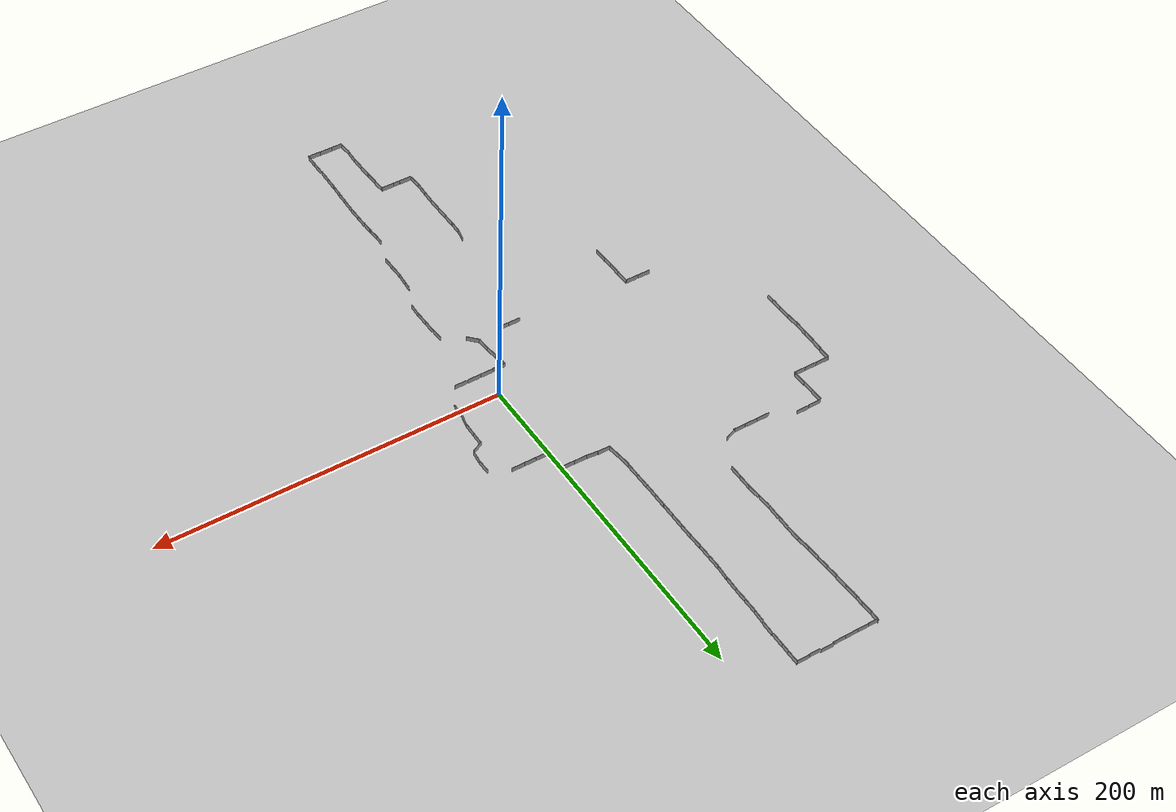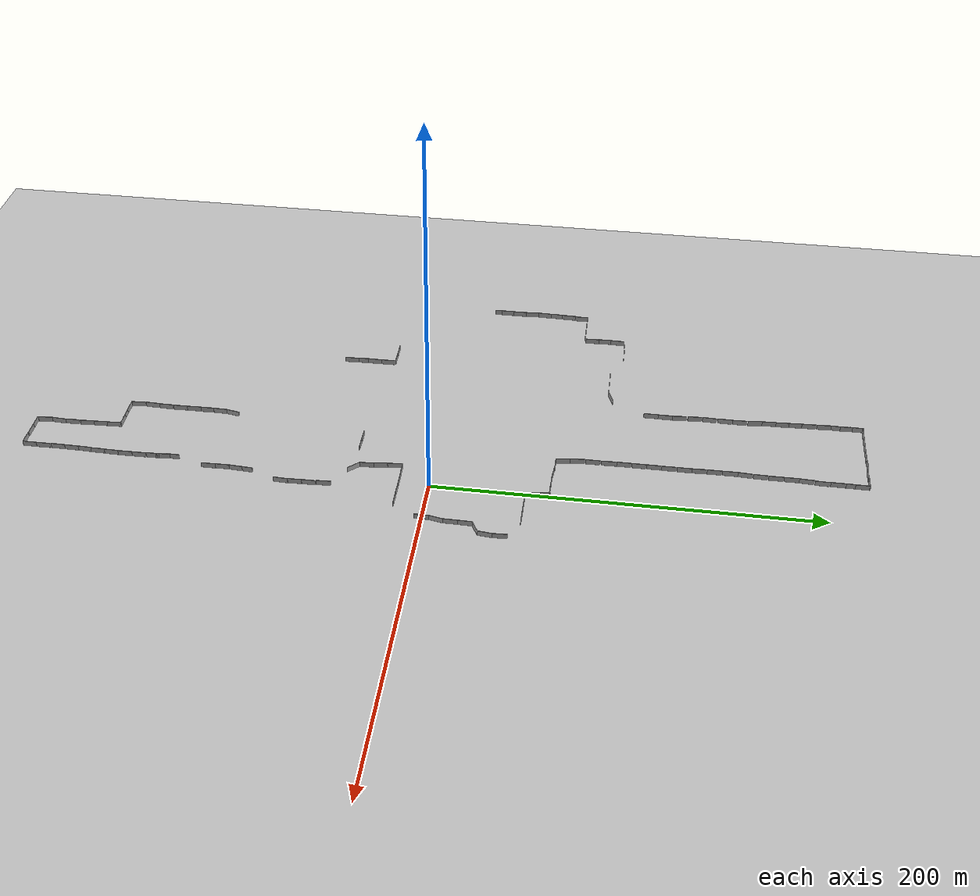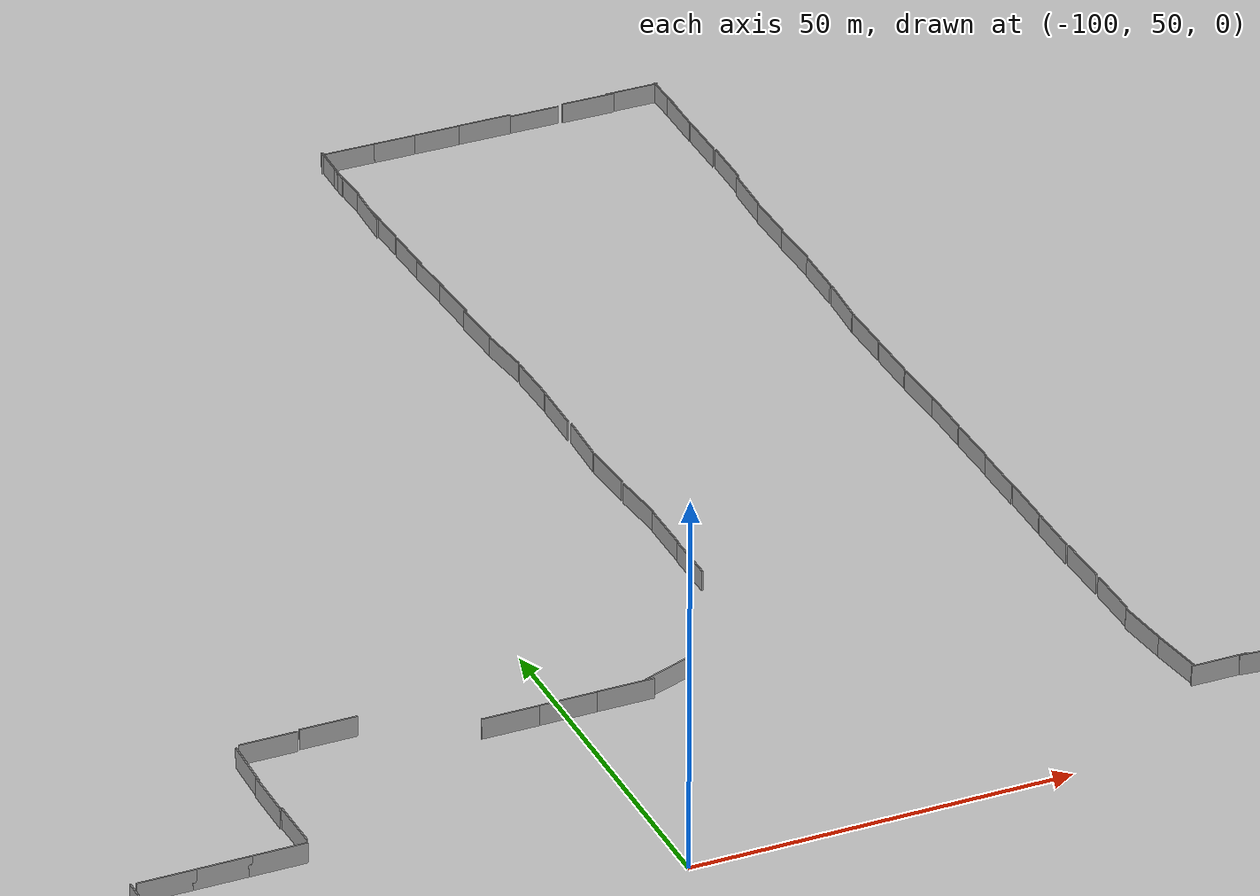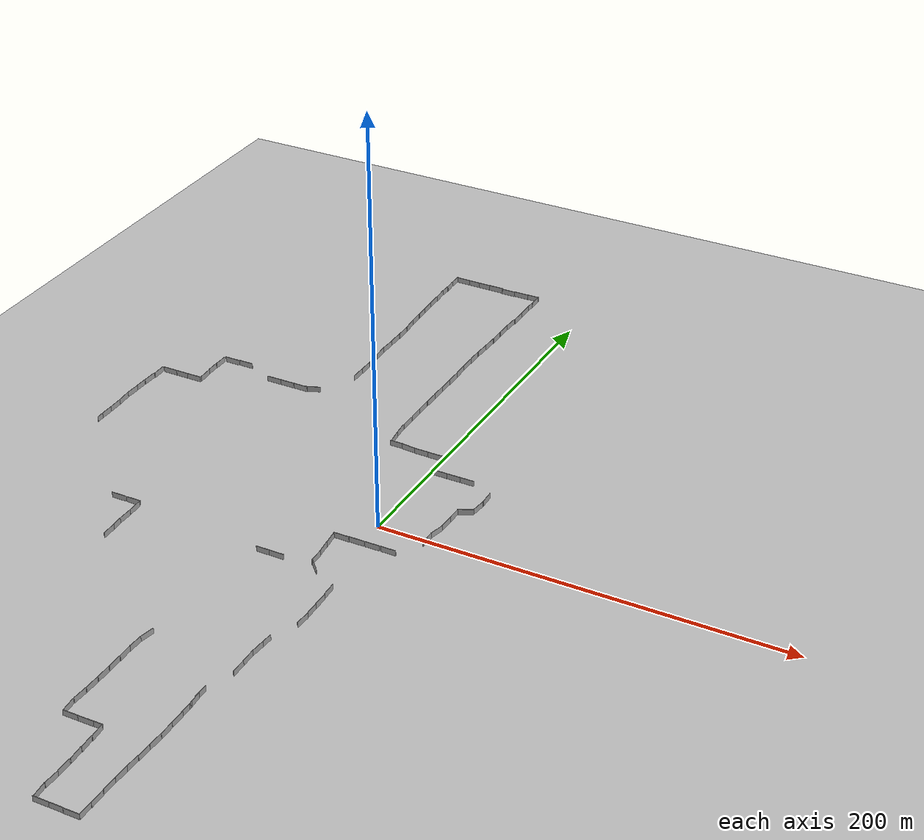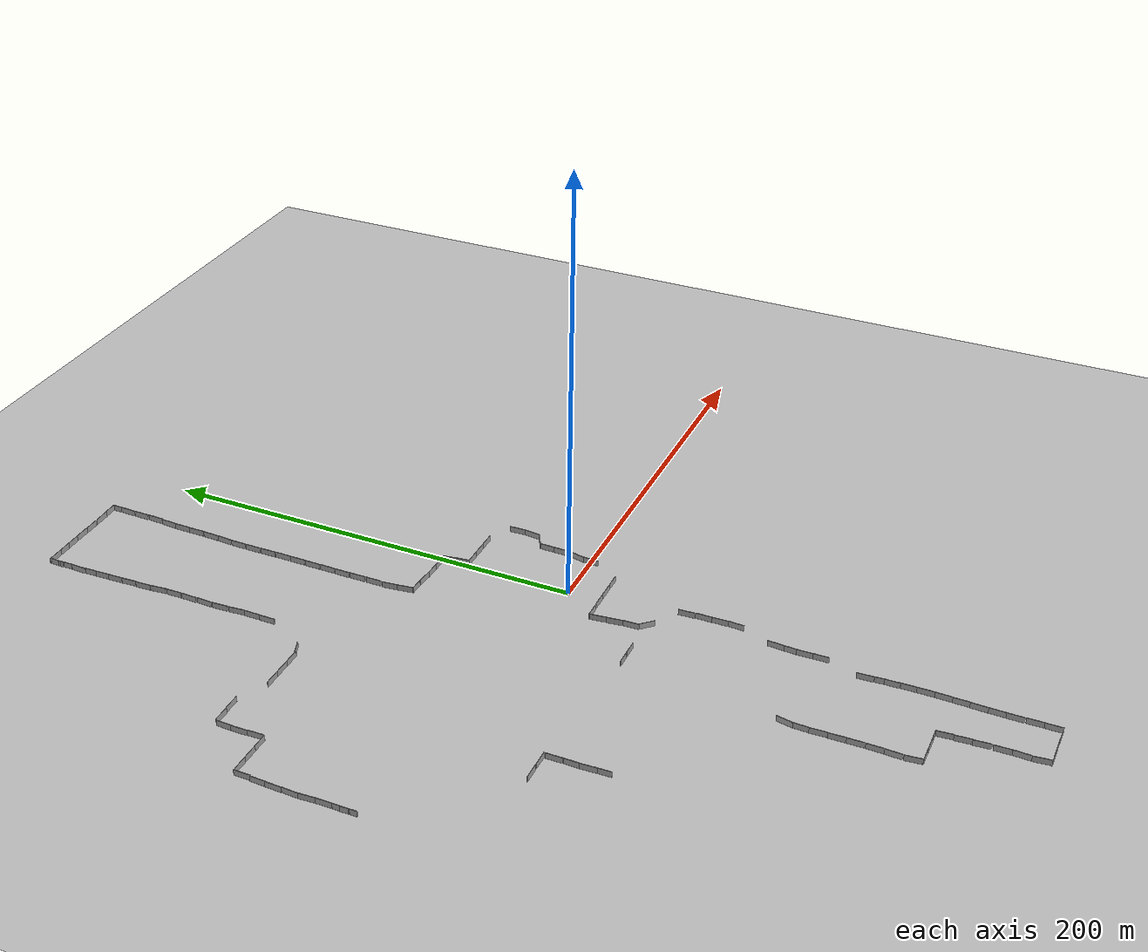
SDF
<sdf version="1.4">
 <world name="default">
  <model name="ground_plane">
   <static>1</static>
   <link name="link">
    <collision name="collision">
     <geometry><plane><normal>0 0 1</normal><size>100 100</size></plane></geometry>
     <surface><friction><ode><mu>100</mu><mu2>50</mu2></ode></friction></surface>
    </collision>
    <visual name="visual">
     <cast_shadows>0</cast_shadows>
     <geometry><plane><normal>0 0 1</normal><size>100 100</size></plane></geometry>
     <material>
      <script><uri>file://media/materials/scripts/gazebo.material</uri><name>Gazebo/Grey</name></script>
     </material>
    </visual>
    <velocity_decay><linear>0</linear><angular>0</angular></velocity_decay>
   </link>
  </model>
  <light name="sun" type="directional">
   <pose>0 0 10 0 -0 0</pose>
   <diffuse>0.8 0.8 0.8 1</diffuse>
   <specular>0.2 0.2 0.2 1</specular>
   <attenuation>
    <range>1000</range>
    <constant>0.9</constant>
    <linear>0.01</linear>
    <quadratic>0.001</quadratic>
   </attenuation>
   <direction>-0.5 0.1 -0.9</direction>
  </light>
  <physics type="ode">
   <max_step_size>0.01</max_step_size>
   <real_time_factor>1</real_time_factor>
   <real_time_update_rate>100</real_time_update_rate>
   <gravity>0 0 -9.8</gravity>
  </physics>
  <scene><ambient>0.4 0.4 0.4 1</ambient><background>0.7 0.7 0.7 1</background><shadows>1</shadows></scene>
  <spherical_coordinates>
   <surface_model>EARTH_WGS84</surface_model>
   <latitude_deg>28.2265</latitude_deg>
   <longitude_deg>112.997</longitude_deg>
   <elevation>41</elevation>
   <heading_deg>0</heading_deg>
  </spherical_coordinates>
  <model name="grey_wall">
   <static>1</static>
   <link name="link">
    <pose>0 0 1.4 0 -0 0</pose>
    <collision name="collision"><geometry><box><size>7.5 0.2 2.8</size></box></geometry></collision>
    <visual name="visual">
     <cast_shadows>0</cast_shadows>
     <geometry><box><size>7.5 0.2 2.8</size></box></geometry>
     <material>
      <script>
       <uri>model://grey_wall/materials/scripts</uri>
       <uri>model://grey_wall/materials/textures</uri>
       <name>vrc/grey_wall</name>
      </script>
     </material>
    </visual>
    <velocity_decay><linear>0</linear><angular>0</angular></velocity_decay>
   </link>
   <pose>-34.2822 -40.4359 0 0 -0 0</pose>
  </model>
  <model name="grey_wall_0">
   <static>1</static>
   <link name="link">
    <pose>0 0 1.4 0 -0 0</pose>
    <collision name="collision"><geometry><box><size>7.5 0.2 2.8</size></box></geometry></collision>
    <visual name="visual">
     <cast_shadows>0</cast_shadows>
     <geometry><box><size>7.5 0.2 2.8</size></box></geometry>
     <material>
      <script>
       <uri>model://grey_wall/materials/scripts</uri>
       <uri>model://grey_wall/materials/textures</uri>
       <name>vrc/grey_wall</name>
      </script>
     </material>
    </visual>
    <velocity_decay><linear>0</linear><angular>0</angular></velocity_decay>
   </link>
   <pose>-27.7399 -40.4579 0 0 -0 0</pose>
  </model>
  <model name="grey_wall_1">
   <static>1</static>
   <link name="link">
    <pose>0 0 1.4 0 -0 0</pose>
    <collision name="collision"><geometry><box><size>7.5 0.2 2.8</size></box></geometry></collision>
    <visual name="visual">
     <cast_shadows>0</cast_shadows>
     <geometry><box><size>7.5 0.2 2.8</size></box></geometry>
     <material>
      <script>
       <uri>model://grey_wall/materials/scripts</uri>
       <uri>model://grey_wall/materials/textures</uri>
       <name>vrc/grey_wall</name>
      </script>
     </material>
    </visual>
    <velocity_decay><linear>0</linear><angular>0</angular></velocity_decay>
   </link>
   <pose>-44.8137 -113.805 0 0 0 -1.76709</pose>
  </model>
  <model name="grey_wall_2">
   <static>1</static>
   <link name="link">
    <pose>0 0 1.4 0 -0 0</pose>
    <collision name="collision"><geometry><box><size>7.5 0.2 2.8</size></box></geometry></collision>
    <visual name="visual">
     <cast_shadows>0</cast_shadows>
     <geometry><box><size>7.5 0.2 2.8</size></box></geometry>
     <material>
      <script>
       <uri>model://grey_wall/materials/scripts</uri>
       <uri>model://grey_wall/materials/textures</uri>
       <name>vrc/grey_wall</name>
      </script>
     </material>
    </visual>
    <velocity_decay><linear>0</linear><angular>0</angular></velocity_decay>
   </link>
   <pose>-8.39449 -40.5188 0 0 0 -0.809937</pose>
  </model>
  <model name="grey_wall_3">
   <static>1</static>
   <link name="link">
    <pose>0 0 1.4 0 -0 0</pose>
    <collision name="collision"><geometry><box><size>7.5 0.2 2.8</size></box></geometry></collision>
    <visual name="visual">
     <cast_shadows>0</cast_shadows>
     <geometry><box><size>7.5 0.2 2.8</size></box></geometry>
     <material>
      <script>
       <uri>model://grey_wall/materials/scripts</uri>
       <uri>model://grey_wall/materials/textures</uri>
       <name>vrc/grey_wall</name>
      </script>
     </material>
    </visual>
    <velocity_decay><linear>0</linear><angular>0</angular></velocity_decay>
   </link>
   <pose>6.24413 -53.131 0 0 0 -1.52108</pose>
  </model>
  <model name="grey_wall_4">
   <static>1</static>
   <link name="link">
    <pose>0 0 1.4 0 -0 0</pose>
    <collision name="collision"><geometry><box><size>7.5 0.2 2.8</size></box></geometry></collision>
    <visual name="visual">
     <cast_shadows>0</cast_shadows>
     <geometry><box><size>7.5 0.2 2.8</size></box></geometry>
     <material>
      <script>
       <uri>model://grey_wall/materials/scripts</uri>
       <uri>model://grey_wall/materials/textures</uri>
       <name>vrc/grey_wall</name>
      </script>
     </material>
    </visual>
    <velocity_decay><linear>0</linear><angular>0</angular></velocity_decay>
   </link>
   <pose>-76.1608 200.541 0 0 0 -1.51664</pose>
  </model>
  <model name="grey_wall_5">
   <static>1</static>
   <link name="link">
    <pose>0 0 1.4 0 -0 0</pose>
    <collision name="collision"><geometry><box><size>7.5 0.2 2.8</size></box></geometry></collision>
    <visual name="visual">
     <cast_shadows>0</cast_shadows>
     <geometry><box><size>7.5 0.2 2.8</size></box></geometry>
     <material>
      <script>
       <uri>model://grey_wall/materials/scripts</uri>
       <uri>model://grey_wall/materials/textures</uri>
       <name>vrc/grey_wall</name>
      </script>
     </material>
    </visual>
    <velocity_decay><linear>0</linear><angular>0</angular></velocity_decay>
   </link>
   <pose>-75.8818 192.67 0 0 0 -1.5318</pose>
  </model>
  <model name="grey_wall_6">
   <static>1</static>
   <link name="link">
    <pose>0 0 1.4 0 -0 0</pose>
    <collision name="collision"><geometry><box><size>7.5 0.2 2.8</size></box></geometry></collision>
    <visual name="visual">
     <cast_shadows>0</cast_shadows>
     <geometry><box><size>7.5 0.2 2.8</size></box></geometry>
     <material>
      <script>
       <uri>model://grey_wall/materials/scripts</uri>
       <uri>model://grey_wall/materials/textures</uri>
       <name>vrc/grey_wall</name>
      </script>
     </material>
    </visual>
    <velocity_decay><linear>0</linear><angular>0</angular></velocity_decay>
   </link>
   <pose>-75.6579 185.97 0 0 0 -1.50708</pose>
  </model>
  <model name="grey_wall_7">
   <static>1</static>
   <link name="link">
    <pose>0 0 1.4 0 -0 0</pose>
    <collision name="collision"><geometry><box><size>7.5 0.2 2.8</size></box></geometry></collision>
    <visual name="visual">
     <cast_shadows>0</cast_shadows>
     <geometry><box><size>7.5 0.2 2.8</size></box></geometry>
     <material>
      <script>
       <uri>model://grey_wall/materials/scripts</uri>
       <uri>model://grey_wall/materials/textures</uri>
       <name>vrc/grey_wall</name>
      </script>
     </material>
    </visual>
    <velocity_decay><linear>0</linear><angular>0</angular></velocity_decay>
   </link>
   <pose>-75.3209 179.09 0 0 0 -1.51077</pose>
  </model>
  <model name="grey_wall_8">
   <static>1</static>
   <link name="link">
    <pose>0 0 1.4 0 -0 0</pose>
    <collision name="collision"><geometry><box><size>7.5 0.2 2.8</size></box></geometry></collision>
    <visual name="visual">
     <cast_shadows>0</cast_shadows>
     <geometry><box><size>7.5 0.2 2.8</size></box></geometry>
     <material>
      <script>
       <uri>model://grey_wall/materials/scripts</uri>
       <uri>model://grey_wall/materials/textures</uri>
       <name>vrc/grey_wall</name>
      </script>
     </material>
    </visual>
    <velocity_decay><linear>0</linear><angular>0</angular></velocity_decay>
   </link>
   <pose>-75.1405 171.723 0 0 0 -1.5146</pose>
  </model>
  <model name="grey_wall_9">
   <static>1</static>
   <link name="link">
    <pose>0 0 1.4 0 -0 0</pose>
    <collision name="collision"><geometry><box><size>7.5 0.2 2.8</size></box></geometry></collision>
    <visual name="visual">
     <cast_shadows>0</cast_shadows>
     <geometry><box><size>7.5 0.2 2.8</size></box></geometry>
     <material>
      <script>
       <uri>model://grey_wall/materials/scripts</uri>
       <uri>model://grey_wall/materials/textures</uri>
       <name>vrc/grey_wall</name>
      </script>
     </material>
    </visual>
    <velocity_decay><linear>0</linear><angular>0</angular></velocity_decay>
   </link>
   <pose>-74.5629 164.279 0 0 0 -1.4614</pose>
  </model>
  <model name="grey_wall_10">
   <static>1</static>
   <link name="link">
    <pose>0 0 1.4 0 -0 0</pose>
    <collision name="collision"><geometry><box><size>7.5 0.2 2.8</size></box></geometry></collision>
    <visual name="visual">
     <cast_shadows>0</cast_shadows>
     <geometry><box><size>7.5 0.2 2.8</size></box></geometry>
     <material>
      <script>
       <uri>model://grey_wall/materials/scripts</uri>
       <uri>model://grey_wall/materials/textures</uri>
       <name>vrc/grey_wall</name>
      </script>
     </material>
    </visual>
    <velocity_decay><linear>0</linear><angular>0</angular></velocity_decay>
   </link>
   <pose>-74.1024 156.293 0 0 0 -1.54552</pose>
  </model>
  <model name="grey_wall_11">
   <static>1</static>
   <link name="link">
    <pose>0 0 1.4 0 -0 0</pose>
    <collision name="collision"><geometry><box><size>7.5 0.2 2.8</size></box></geometry></collision>
    <visual name="visual">
     <cast_shadows>0</cast_shadows>
     <geometry><box><size>7.5 0.2 2.8</size></box></geometry>
     <material>
      <script>
       <uri>model://grey_wall/materials/scripts</uri>
       <uri>model://grey_wall/materials/textures</uri>
       <name>vrc/grey_wall</name>
      </script>
     </material>
    </visual>
    <velocity_decay><linear>0</linear><angular>0</angular></velocity_decay>
   </link>
   <pose>-74.1104 148.456 0 0 0 -1.58822</pose>
  </model>
  <model name="grey_wall_12">
   <static>1</static>
   <link name="link">
    <pose>0 0 1.4 0 -0 0</pose>
    <collision name="collision"><geometry><box><size>7.5 0.2 2.8</size></box></geometry></collision>
    <visual name="visual">
     <cast_shadows>0</cast_shadows>
     <geometry><box><size>7.5 0.2 2.8</size></box></geometry>
     <material>
      <script>
       <uri>model://grey_wall/materials/scripts</uri>
       <uri>model://grey_wall/materials/textures</uri>
       <name>vrc/grey_wall</name>
      </script>
     </material>
    </visual>
    <velocity_decay><linear>0</linear><angular>0</angular></velocity_decay>
   </link>
   <pose>-74.1605 140.333 0 0 0 -1.60894</pose>
  </model>
  <model name="grey_wall_13">
   <static>1</static>
   <link name="link">
    <pose>0 0 1.4 0 -0 0</pose>
    <collision name="collision"><geometry><box><size>7.5 0.2 2.8</size></box></geometry></collision>
    <visual name="visual">
     <cast_shadows>0</cast_shadows>
     <geometry><box><size>7.5 0.2 2.8</size></box></geometry>
     <material>
      <script>
       <uri>model://grey_wall/materials/scripts</uri>
       <uri>model://grey_wall/materials/textures</uri>
       <name>vrc/grey_wall</name>
      </script>
     </material>
    </visual>
    <velocity_decay><linear>0</linear><angular>0</angular></velocity_decay>
   </link>
   <pose>-74.0532 132.481 0 0 0 -1.51366</pose>
  </model>
  <model name="grey_wall_14">
   <static>1</static>
   <link name="link">
    <pose>0 0 1.4 0 -0 0</pose>
    <collision name="collision"><geometry><box><size>7.5 0.2 2.8</size></box></geometry></collision>
    <visual name="visual">
     <cast_shadows>0</cast_shadows>
     <geometry><box><size>7.5 0.2 2.8</size></box></geometry>
     <material>
      <script>
       <uri>model://grey_wall/materials/scripts</uri>
       <uri>model://grey_wall/materials/textures</uri>
       <name>vrc/grey_wall</name>
      </script>
     </material>
    </visual>
    <velocity_decay><linear>0</linear><angular>0</angular></velocity_decay>
   </link>
   <pose>-73.5097 124.393 0 0 0 -1.47887</pose>
  </model>
  <model name="grey_wall_15">
   <static>1</static>
   <link name="link">
    <pose>0 0 1.4 0 -0 0</pose>
    <collision name="collision"><geometry><box><size>7.5 0.2 2.8</size></box></geometry></collision>
    <visual name="visual">
     <cast_shadows>0</cast_shadows>
     <geometry><box><size>7.5 0.2 2.8</size></box></geometry>
     <material>
      <script>
       <uri>model://grey_wall/materials/scripts</uri>
       <uri>model://grey_wall/materials/textures</uri>
       <name>vrc/grey_wall</name>
      </script>
     </material>
    </visual>
    <velocity_decay><linear>0</linear><angular>0</angular></velocity_decay>
   </link>
   <pose>-73.289 116.743 0 0 0 -1.57441</pose>
  </model>
  <model name="grey_wall_16">
   <static>1</static>
   <link name="link">
    <pose>0 0 1.4 0 -0 0</pose>
    <collision name="collision"><geometry><box><size>7.5 0.2 2.8</size></box></geometry></collision>
    <visual name="visual">
     <cast_shadows>0</cast_shadows>
     <geometry><box><size>7.5 0.2 2.8</size></box></geometry>
     <material>
      <script>
       <uri>model://grey_wall/materials/scripts</uri>
       <uri>model://grey_wall/materials/textures</uri>
       <name>vrc/grey_wall</name>
      </script>
     </material>
    </visual>
    <velocity_decay><linear>0</linear><angular>0</angular></velocity_decay>
   </link>
   <pose>-73.3762 109.085 0 0 0 -1.56903</pose>
  </model>
  <model name="grey_wall_17">
   <static>1</static>
   <link name="link">
    <pose>0 0 1.4 0 -0 0</pose>
    <collision name="collision"><geometry><box><size>7.5 0.2 2.8</size></box></geometry></collision>
    <visual name="visual">
     <cast_shadows>0</cast_shadows>
     <geometry><box><size>7.5 0.2 2.8</size></box></geometry>
     <material>
      <script>
       <uri>model://grey_wall/materials/scripts</uri>
       <uri>model://grey_wall/materials/textures</uri>
       <name>vrc/grey_wall</name>
      </script>
     </material>
    </visual>
    <velocity_decay><linear>0</linear><angular>0</angular></velocity_decay>
   </link>
   <pose>-29.7776 158.602 0 0 0 -1.64072</pose>
  </model>
  <model name="grey_wall_18">
   <static>1</static>
   <link name="link">
    <pose>0 0 1.4 0 -0 0</pose>
    <collision name="collision"><geometry><box><size>7.5 0.2 2.8</size></box></geometry></collision>
    <visual name="visual">
     <cast_shadows>0</cast_shadows>
     <geometry><box><size>7.5 0.2 2.8</size></box></geometry>
     <material>
      <script>
       <uri>model://grey_wall/materials/scripts</uri>
       <uri>model://grey_wall/materials/textures</uri>
       <name>vrc/grey_wall</name>
      </script>
     </material>
    </visual>
    <velocity_decay><linear>0</linear><angular>0</angular></velocity_decay>
   </link>
   <pose>-28.5389 205.136 0 0 0 -1.5832</pose>
  </model>
  <model name="grey_wall_19">
   <static>1</static>
   <link name="link">
    <pose>0 0 1.4 0 -0 0</pose>
    <collision name="collision"><geometry><box><size>7.5 0.2 2.8</size></box></geometry></collision>
    <visual name="visual">
     <cast_shadows>0</cast_shadows>
     <geometry><box><size>7.5 0.2 2.8</size></box></geometry>
     <material>
      <script>
       <uri>model://grey_wall/materials/scripts</uri>
       <uri>model://grey_wall/materials/textures</uri>
       <name>vrc/grey_wall</name>
      </script>
     </material>
    </visual>
    <velocity_decay><linear>0</linear><angular>0</angular></velocity_decay>
   </link>
   <pose>-28.496 197.316 0 0 0 -1.59459</pose>
  </model>
  <model name="grey_wall_20">
   <static>1</static>
   <link name="link">
    <pose>0 0 1.4 0 -0 0</pose>
    <collision name="collision"><geometry><box><size>7.5 0.2 2.8</size></box></geometry></collision>
    <visual name="visual">
     <cast_shadows>0</cast_shadows>
     <geometry><box><size>7.5 0.2 2.8</size></box></geometry>
     <material>
      <script>
       <uri>model://grey_wall/materials/scripts</uri>
       <uri>model://grey_wall/materials/textures</uri>
       <name>vrc/grey_wall</name>
      </script>
     </material>
    </visual>
    <velocity_decay><linear>0</linear><angular>0</angular></velocity_decay>
   </link>
   <pose>-29.065 189.456 0 0 0 -1.61877</pose>
  </model>
  <model name="grey_wall_21">
   <static>1</static>
   <link name="link">
    <pose>0 0 1.4 0 -0 0</pose>
    <collision name="collision"><geometry><box><size>7.5 0.2 2.8</size></box></geometry></collision>
    <visual name="visual">
     <cast_shadows>0</cast_shadows>
     <geometry><box><size>7.5 0.2 2.8</size></box></geometry>
     <material>
      <script>
       <uri>model://grey_wall/materials/scripts</uri>
       <uri>model://grey_wall/materials/textures</uri>
       <name>vrc/grey_wall</name>
      </script>
     </material>
    </visual>
    <velocity_decay><linear>0</linear><angular>0</angular></velocity_decay>
   </link>
   <pose>-29.3033 181.863 0 0 0 -1.56661</pose>
  </model>
  <model name="grey_wall_22">
   <static>1</static>
   <link name="link">
    <pose>0 0 1.4 0 -0 0</pose>
    <collision name="collision"><geometry><box><size>7.5 0.2 2.8</size></box></geometry></collision>
    <visual name="visual">
     <cast_shadows>0</cast_shadows>
     <geometry><box><size>7.5 0.2 2.8</size></box></geometry>
     <material>
      <script>
       <uri>model://grey_wall/materials/scripts</uri>
       <uri>model://grey_wall/materials/textures</uri>
       <name>vrc/grey_wall</name>
      </script>
     </material>
    </visual>
    <velocity_decay><linear>0</linear><angular>0</angular></velocity_decay>
   </link>
   <pose>-29.3139 174.168 0 0 0 -1.5502</pose>
  </model>
  <model name="grey_wall_23">
   <static>1</static>
   <link name="link">
    <pose>0 0 1.4 0 -0 0</pose>
    <collision name="collision"><geometry><box><size>7.5 0.2 2.8</size></box></geometry></collision>
    <visual name="visual">
     <cast_shadows>0</cast_shadows>
     <geometry><box><size>7.5 0.2 2.8</size></box></geometry>
     <material>
      <script>
       <uri>model://grey_wall/materials/scripts</uri>
       <uri>model://grey_wall/materials/textures</uri>
       <name>vrc/grey_wall</name>
      </script>
     </material>
    </visual>
    <velocity_decay><linear>0</linear><angular>0</angular></velocity_decay>
   </link>
   <pose>-29.4527 166.419 0 0 0 -1.59655</pose>
  </model>
  <model name="grey_wall_24">
   <static>1</static>
   <link name="link">
    <pose>0 0 1.4 0 -0 0</pose>
    <collision name="collision"><geometry><box><size>7.5 0.2 2.8</size></box></geometry></collision>
    <visual name="visual">
     <cast_shadows>0</cast_shadows>
     <geometry><box><size>7.5 0.2 2.8</size></box></geometry>
     <material>
      <script>
       <uri>model://grey_wall/materials/scripts</uri>
       <uri>model://grey_wall/materials/textures</uri>
       <name>vrc/grey_wall</name>
      </script>
     </material>
    </visual>
    <velocity_decay><linear>0</linear><angular>0</angular></velocity_decay>
   </link>
   <pose>-30.0088 150.9 0 0 0 -1.56181</pose>
  </model>
  <model name="grey_wall_25">
   <static>1</static>
   <link name="link">
    <pose>0 0 1.4 0 -0 0</pose>
    <collision name="collision"><geometry><box><size>7.5 0.2 2.8</size></box></geometry></collision>
    <visual name="visual">
     <cast_shadows>0</cast_shadows>
     <geometry><box><size>7.5 0.2 2.8</size></box></geometry>
     <material>
      <script>
       <uri>model://grey_wall/materials/scripts</uri>
       <uri>model://grey_wall/materials/textures</uri>
       <name>vrc/grey_wall</name>
      </script>
     </material>
    </visual>
    <velocity_decay><linear>0</linear><angular>0</angular></velocity_decay>
   </link>
   <pose>-29.9713 143.125 0 0 0 -1.56389</pose>
  </model>
  <model name="grey_wall_26">
   <static>1</static>
   <link name="link">
    <pose>0 0 1.4 0 -0 0</pose>
    <collision name="collision"><geometry><box><size>7.5 0.2 2.8</size></box></geometry></collision>
    <visual name="visual">
     <cast_shadows>0</cast_shadows>
     <geometry><box><size>7.5 0.2 2.8</size></box></geometry>
     <material>
      <script>
       <uri>model://grey_wall/materials/scripts</uri>
       <uri>model://grey_wall/materials/textures</uri>
       <name>vrc/grey_wall</name>
      </script>
     </material>
    </visual>
    <velocity_decay><linear>0</linear><angular>0</angular></velocity_decay>
   </link>
   <pose>-29.8348 135.39 0 0 0 -1.54202</pose>
  </model>
  <model name="grey_wall_27">
   <static>1</static>
   <link name="link">
    <pose>0 0 1.4 0 -0 0</pose>
    <collision name="collision"><geometry><box><size>7.5 0.2 2.8</size></box></geometry></collision>
    <visual name="visual">
     <cast_shadows>0</cast_shadows>
     <geometry><box><size>7.5 0.2 2.8</size></box></geometry>
     <material>
      <script>
       <uri>model://grey_wall/materials/scripts</uri>
       <uri>model://grey_wall/materials/textures</uri>
       <name>vrc/grey_wall</name>
      </script>
     </material>
    </visual>
    <velocity_decay><linear>0</linear><angular>0</angular></velocity_decay>
   </link>
   <pose>-29.6885 127.817 0 0 0 -1.56994</pose>
  </model>
  <model name="grey_wall_28">
   <static>1</static>
   <link name="link">
    <pose>0 0 1.4 0 -0 0</pose>
    <collision name="collision"><geometry><box><size>7.5 0.2 2.8</size></box></geometry></collision>
    <visual name="visual">
     <cast_shadows>0</cast_shadows>
     <geometry><box><size>7.5 0.2 2.8</size></box></geometry>
     <material>
      <script>
       <uri>model://grey_wall/materials/scripts</uri>
       <uri>model://grey_wall/materials/textures</uri>
       <name>vrc/grey_wall</name>
      </script>
     </material>
    </visual>
    <velocity_decay><linear>0</linear><angular>0</angular></velocity_decay>
   </link>
   <pose>-29.6942 119.998 0 0 0 -1.55973</pose>
  </model>
  <model name="grey_wall_29">
   <static>1</static>
   <link name="link">
    <pose>0 0 1.4 0 -0 0</pose>
    <collision name="collision"><geometry><box><size>7.5 0.2 2.8</size></box></geometry></collision>
    <visual name="visual">
     <cast_shadows>0</cast_shadows>
     <geometry><box><size>7.5 0.2 2.8</size></box></geometry>
     <material>
      <script>
       <uri>model://grey_wall/materials/scripts</uri>
       <uri>model://grey_wall/materials/textures</uri>
       <name>vrc/grey_wall</name>
      </script>
     </material>
    </visual>
    <velocity_decay><linear>0</linear><angular>0</angular></velocity_decay>
   </link>
   <pose>-29.7646 112.252 0 0 0 -1.57293</pose>
  </model>
  <model name="grey_wall_30">
   <static>1</static>
   <link name="link">
    <pose>0 0 1.4 0 -0 0</pose>
    <collision name="collision"><geometry><box><size>7.5 0.2 2.8</size></box></geometry></collision>
    <visual name="visual">
     <cast_shadows>0</cast_shadows>
     <geometry><box><size>7.5 0.2 2.8</size></box></geometry>
     <material>
      <script>
       <uri>model://grey_wall/materials/scripts</uri>
       <uri>model://grey_wall/materials/textures</uri>
       <name>vrc/grey_wall</name>
      </script>
     </material>
    </visual>
    <velocity_decay><linear>0</linear><angular>0</angular></velocity_decay>
   </link>
   <pose>-29.7043 104.62 0 0 0 -1.57915</pose>
  </model>
  <model name="grey_wall_31">
   <static>1</static>
   <link name="link">
    <pose>0 0 1.4 0 -0 0</pose>
    <collision name="collision"><geometry><box><size>7.5 0.2 2.8</size></box></geometry></collision>
    <visual name="visual">
     <cast_shadows>0</cast_shadows>
     <geometry><box><size>7.5 0.2 2.8</size></box></geometry>
     <material>
      <script>
       <uri>model://grey_wall/materials/scripts</uri>
       <uri>model://grey_wall/materials/textures</uri>
       <name>vrc/grey_wall</name>
      </script>
     </material>
    </visual>
    <velocity_decay><linear>0</linear><angular>0</angular></velocity_decay>
   </link>
   <pose>-29.7791 96.9184 0 0 0 -1.57414</pose>
  </model>
  <model name="grey_wall_32">
   <static>1</static>
   <link name="link">
    <pose>0 0 1.4 0 -0 0</pose>
    <collision name="collision"><geometry><box><size>7.5 0.2 2.8</size></box></geometry></collision>
    <visual name="visual">
     <cast_shadows>0</cast_shadows>
     <geometry><box><size>7.5 0.2 2.8</size></box></geometry>
     <material>
      <script>
       <uri>model://grey_wall/materials/scripts</uri>
       <uri>model://grey_wall/materials/textures</uri>
       <name>vrc/grey_wall</name>
      </script>
     </material>
    </visual>
    <velocity_decay><linear>0</linear><angular>0</angular></velocity_decay>
   </link>
   <pose>-29.618 89.0556 0 0 0 -1.55253</pose>
  </model>
  <model name="grey_wall_33">
   <static>1</static>
   <link name="link">
    <pose>0 0 1.4 0 -0 0</pose>
    <collision name="collision"><geometry><box><size>7.5 0.2 2.8</size></box></geometry></collision>
    <visual name="visual">
     <cast_shadows>0</cast_shadows>
     <geometry><box><size>7.5 0.2 2.8</size></box></geometry>
     <material>
      <script>
       <uri>model://grey_wall/materials/scripts</uri>
       <uri>model://grey_wall/materials/textures</uri>
       <name>vrc/grey_wall</name>
      </script>
     </material>
    </visual>
    <velocity_decay><linear>0</linear><angular>0</angular></velocity_decay>
   </link>
   <pose>-29.5264 80.9508 0 0 0 -1.56484</pose>
  </model>
  <model name="grey_wall_34">
   <static>1</static>
   <link name="link">
    <pose>0 0 1.4 0 -0 0</pose>
    <collision name="collision"><geometry><box><size>7.5 0.2 2.8</size></box></geometry></collision>
    <visual name="visual">
     <cast_shadows>0</cast_shadows>
     <geometry><box><size>7.5 0.2 2.8</size></box></geometry>
     <material>
      <script>
       <uri>model://grey_wall/materials/scripts</uri>
       <uri>model://grey_wall/materials/textures</uri>
       <name>vrc/grey_wall</name>
      </script>
     </material>
    </visual>
    <velocity_decay><linear>0</linear><angular>0</angular></velocity_decay>
   </link>
   <pose>-4.19064 61.0198 0 0 -0 0</pose>
  </model>
  <model name="grey_wall_35">
   <static>1</static>
   <link name="link">
    <pose>0 0 1.4 0 -0 0</pose>
    <collision name="collision"><geometry><box><size>7.5 0.2 2.8</size></box></geometry></collision>
    <visual name="visual">
     <cast_shadows>0</cast_shadows>
     <geometry><box><size>7.5 0.2 2.8</size></box></geometry>
     <material>
      <script>
       <uri>model://grey_wall/materials/scripts</uri>
       <uri>model://grey_wall/materials/textures</uri>
       <name>vrc/grey_wall</name>
      </script>
     </material>
    </visual>
    <velocity_decay><linear>0</linear><angular>0</angular></velocity_decay>
   </link>
   <pose>0.004015 57.8546 0 0 0 -1.45444</pose>
  </model>
  <model name="grey_wall_36">
   <static>1</static>
   <link name="link">
    <pose>0 0 1.4 0 -0 0</pose>
    <collision name="collision"><geometry><box><size>7.5 0.2 2.8</size></box></geometry></collision>
    <visual name="visual">
     <cast_shadows>0</cast_shadows>
     <geometry><box><size>7.5 0.2 2.8</size></box></geometry>
     <material>
      <script>
       <uri>model://grey_wall/materials/scripts</uri>
       <uri>model://grey_wall/materials/textures</uri>
       <name>vrc/grey_wall</name>
      </script>
     </material>
    </visual>
    <velocity_decay><linear>0</linear><angular>0</angular></velocity_decay>
   </link>
   <pose>-18.191 61.5339 0 0 -0 3.04974</pose>
  </model>
  <model name="grey_wall_37">
   <static>1</static>
   <link name="link">
    <pose>0 0 1.4 0 -0 0</pose>
    <collision name="collision"><geometry><box><size>7.5 0.2 2.8</size></box></geometry></collision>
    <visual name="visual">
     <cast_shadows>0</cast_shadows>
     <geometry><box><size>7.5 0.2 2.8</size></box></geometry>
     <material>
      <script>
       <uri>model://grey_wall/materials/scripts</uri>
       <uri>model://grey_wall/materials/textures</uri>
       <name>vrc/grey_wall</name>
      </script>
     </material>
    </visual>
    <velocity_decay><linear>0</linear><angular>0</angular></velocity_decay>
   </link>
   <pose>-29.3205 73.0497 0 0 0 -1.46343</pose>
  </model>
  <model name="grey_wall_38">
   <static>1</static>
   <link name="link">
    <pose>0 0 1.4 0 -0 0</pose>
    <collision name="collision"><geometry><box><size>7.5 0.2 2.8</size></box></geometry></collision>
    <visual name="visual">
     <cast_shadows>0</cast_shadows>
     <geometry><box><size>7.5 0.2 2.8</size></box></geometry>
     <material>
      <script>
       <uri>model://grey_wall/materials/scripts</uri>
       <uri>model://grey_wall/materials/textures</uri>
       <name>vrc/grey_wall</name>
      </script>
     </material>
    </visual>
    <velocity_decay><linear>0</linear><angular>0</angular></velocity_decay>
   </link>
   <pose>-11.0667 61.1316 0 0 -0 0</pose>
  </model>
  <model name="grey_wall_39">
   <static>1</static>
   <link name="link">
    <pose>0 0 1.4 0 -0 0</pose>
    <collision name="collision"><geometry><box><size>7.5 0.2 2.8</size></box></geometry></collision>
    <visual name="visual">
     <cast_shadows>0</cast_shadows>
     <geometry><box><size>7.5 0.2 2.8</size></box></geometry>
     <material>
      <script>
       <uri>model://grey_wall/materials/scripts</uri>
       <uri>model://grey_wall/materials/textures</uri>
       <name>vrc/grey_wall</name>
      </script>
     </material>
    </visual>
    <velocity_decay><linear>0</linear><angular>0</angular></velocity_decay>
   </link>
   <pose>-107.514 85.4018 0 0 -0 0</pose>
  </model>
  <model name="grey_wall_40">
   <static>1</static>
   <link name="link">
    <pose>0 0 1.4 0 -0 0</pose>
    <collision name="collision"><geometry><box><size>7.5 0.2 2.8</size></box></geometry></collision>
    <visual name="visual">
     <cast_shadows>0</cast_shadows>
     <geometry><box><size>7.5 0.2 2.8</size></box></geometry>
     <material>
      <script>
       <uri>model://grey_wall/materials/scripts</uri>
       <uri>model://grey_wall/materials/textures</uri>
       <name>vrc/grey_wall</name>
      </script>
     </material>
    </visual>
    <velocity_decay><linear>0</linear><angular>0</angular></velocity_decay>
   </link>
   <pose>-100 85.4362 0 0 -0 0</pose>
  </model>
  <model name="grey_wall_41">
   <static>1</static>
   <link name="link">
    <pose>0 0 1.4 0 -0 0</pose>
    <collision name="collision"><geometry><box><size>7.5 0.2 2.8</size></box></geometry></collision>
    <visual name="visual">
     <cast_shadows>0</cast_shadows>
     <geometry><box><size>7.5 0.2 2.8</size></box></geometry>
     <material>
      <script>
       <uri>model://grey_wall/materials/scripts</uri>
       <uri>model://grey_wall/materials/textures</uri>
       <name>vrc/grey_wall</name>
      </script>
     </material>
    </visual>
    <velocity_decay><linear>0</linear><angular>0</angular></velocity_decay>
   </link>
   <pose>-92.4141 85.4631 0 0 -0 0</pose>
  </model>
  <model name="grey_wall_42">
   <static>1</static>
   <link name="link">
    <pose>0 0 1.4 0 -0 0</pose>
    <collision name="collision"><geometry><box><size>7.5 0.2 2.8</size></box></geometry></collision>
    <visual name="visual">
     <cast_shadows>0</cast_shadows>
     <geometry><box><size>7.5 0.2 2.8</size></box></geometry>
     <material>
      <script>
       <uri>model://grey_wall/materials/scripts</uri>
       <uri>model://grey_wall/materials/textures</uri>
       <name>vrc/grey_wall</name>
      </script>
     </material>
    </visual>
    <velocity_decay><linear>0</linear><angular>0</angular></velocity_decay>
   </link>
   <pose>-86.2211 86.9086 0 0 -0 0.353572</pose>
  </model>
  <model name="grey_wall_43">
   <static>1</static>
   <link name="link">
    <pose>0 0 1.4 0 -0 0</pose>
    <collision name="collision"><geometry><box><size>7.5 0.2 2.8</size></box></geometry></collision>
    <visual name="visual">
     <cast_shadows>0</cast_shadows>
     <geometry><box><size>7.5 0.2 2.8</size></box></geometry>
     <material>
      <script>
       <uri>model://grey_wall/materials/scripts</uri>
       <uri>model://grey_wall/materials/textures</uri>
       <name>vrc/grey_wall</name>
      </script>
     </material>
    </visual>
    <velocity_decay><linear>0</linear><angular>0</angular></velocity_decay>
   </link>
   <pose>-53.3455 220.702 0 0 -0 0</pose>
  </model>
  <model name="grey_wall_44">
   <static>1</static>
   <link name="link">
    <pose>0 0 1.4 0 -0 0</pose>
    <collision name="collision"><geometry><box><size>7.5 0.2 2.8</size></box></geometry></collision>
    <visual name="visual">
     <cast_shadows>0</cast_shadows>
     <geometry><box><size>7.5 0.2 2.8</size></box></geometry>
     <material>
      <script>
       <uri>model://grey_wall/materials/scripts</uri>
       <uri>model://grey_wall/materials/textures</uri>
       <name>vrc/grey_wall</name>
      </script>
     </material>
    </visual>
    <velocity_decay><linear>0</linear><angular>0</angular></velocity_decay>
   </link>
   <pose>-46.1884 221.037 -0.462886 0 -0 0</pose>
  </model>
  <model name="grey_wall_45">
   <static>1</static>
   <link name="link">
    <pose>0 0 1.4 0 -0 0</pose>
    <collision name="collision"><geometry><box><size>7.5 0.2 2.8</size></box></geometry></collision>
    <visual name="visual">
     <cast_shadows>0</cast_shadows>
     <geometry><box><size>7.5 0.2 2.8</size></box></geometry>
     <material>
      <script>
       <uri>model://grey_wall/materials/scripts</uri>
       <uri>model://grey_wall/materials/textures</uri>
       <name>vrc/grey_wall</name>
      </script>
     </material>
    </visual>
    <velocity_decay><linear>0</linear><angular>0</angular></velocity_decay>
   </link>
   <pose>-38.313 220.604 0 0 -0 0</pose>
  </model>
  <model name="grey_wall_46">
   <static>1</static>
   <link name="link">
    <pose>0 0 1.4 0 -0 0</pose>
    <collision name="collision"><geometry><box><size>7.5 0.2 2.8</size></box></geometry></collision>
    <visual name="visual">
     <cast_shadows>0</cast_shadows>
     <geometry><box><size>7.5 0.2 2.8</size></box></geometry>
     <material>
      <script>
       <uri>model://grey_wall/materials/scripts</uri>
       <uri>model://grey_wall/materials/textures</uri>
       <name>vrc/grey_wall</name>
      </script>
     </material>
    </visual>
    <velocity_decay><linear>0</linear><angular>0</angular></velocity_decay>
   </link>
   <pose>-60.7482 220.647 0 0 -0 0</pose>
  </model>
  <model name="grey_wall_47">
   <static>1</static>
   <link name="link">
    <pose>0 0 1.4 0 -0 0</pose>
    <collision name="collision"><geometry><box><size>7.5 0.2 2.8</size></box></geometry></collision>
    <visual name="visual">
     <cast_shadows>0</cast_shadows>
     <geometry><box><size>7.5 0.2 2.8</size></box></geometry>
     <material>
      <script>
       <uri>model://grey_wall/materials/scripts</uri>
       <uri>model://grey_wall/materials/textures</uri>
       <name>vrc/grey_wall</name>
      </script>
     </material>
    </visual>
    <velocity_decay><linear>0</linear><angular>0</angular></velocity_decay>
   </link>
   <pose>-67.1582 220.621 0 0 -0 0</pose>
  </model>
  <model name="grey_wall_48">
   <static>1</static>
   <link name="link">
    <pose>0 0 1.4 0 -0 0</pose>
    <collision name="collision"><geometry><box><size>7.5 0.2 2.8</size></box></geometry></collision>
    <visual name="visual">
     <cast_shadows>0</cast_shadows>
     <geometry><box><size>7.5 0.2 2.8</size></box></geometry>
     <material>
      <script>
       <uri>model://grey_wall/materials/scripts</uri>
       <uri>model://grey_wall/materials/textures</uri>
       <name>vrc/grey_wall</name>
      </script>
     </material>
    </visual>
    <velocity_decay><linear>0</linear><angular>0</angular></velocity_decay>
   </link>
   <pose>-72.9286 220.618 0 0 -0 0</pose>
  </model>
  <model name="grey_wall_49">
   <static>1</static>
   <link name="link">
    <pose>0 0 1.4 0 -0 0</pose>
    <collision name="collision"><geometry><box><size>7.5 0.2 2.8</size></box></geometry></collision>
    <visual name="visual">
     <cast_shadows>0</cast_shadows>
     <geometry><box><size>7.5 0.2 2.8</size></box></geometry>
     <material>
      <script>
       <uri>model://grey_wall/materials/scripts</uri>
       <uri>model://grey_wall/materials/textures</uri>
       <name>vrc/grey_wall</name>
      </script>
     </material>
    </visual>
    <velocity_decay><linear>0</linear><angular>0</angular></velocity_decay>
   </link>
   <pose>-31.8845 220.774 0 0 -0 0</pose>
  </model>
  <model name="grey_wall_50">
   <static>1</static>
   <link name="link">
    <pose>0 0 1.4 0 -0 0</pose>
    <collision name="collision"><geometry><box><size>7.5 0.2 2.8</size></box></geometry></collision>
    <visual name="visual">
     <cast_shadows>0</cast_shadows>
     <geometry><box><size>7.5 0.2 2.8</size></box></geometry>
     <material>
      <script>
       <uri>model://grey_wall/materials/scripts</uri>
       <uri>model://grey_wall/materials/textures</uri>
       <name>vrc/grey_wall</name>
      </script>
     </material>
    </visual>
    <velocity_decay><linear>0</linear><angular>0</angular></velocity_decay>
   </link>
   <pose>-76.3449 205.48 0 0 0 -1.60769</pose>
  </model>
  <model name="grey_wall_51">
   <static>1</static>
   <link name="link">
    <pose>0 0 1.4 0 -0 0</pose>
    <collision name="collision"><geometry><box><size>7.5 0.2 2.8</size></box></geometry></collision>
    <visual name="visual">
     <cast_shadows>0</cast_shadows>
     <geometry><box><size>7.5 0.2 2.8</size></box></geometry>
     <material>
      <script>
       <uri>model://grey_wall/materials/scripts</uri>
       <uri>model://grey_wall/materials/textures</uri>
       <name>vrc/grey_wall</name>
      </script>
     </material>
    </visual>
    <velocity_decay><linear>0</linear><angular>0</angular></velocity_decay>
   </link>
   <pose>25.8102 7.11222 0 0 0 -1.79061</pose>
  </model>
  <model name="grey_wall_52">
   <static>1</static>
   <link name="link">
    <pose>0 0 1.4 0 -0 0</pose>
    <collision name="collision"><geometry><box><size>7.5 0.2 2.8</size></box></geometry></collision>
    <visual name="visual">
     <cast_shadows>0</cast_shadows>
     <geometry><box><size>7.5 0.2 2.8</size></box></geometry>
     <material>
      <script>
       <uri>model://grey_wall/materials/scripts</uri>
       <uri>model://grey_wall/materials/textures</uri>
       <name>vrc/grey_wall</name>
      </script>
     </material>
    </visual>
    <velocity_decay><linear>0</linear><angular>0</angular></velocity_decay>
   </link>
   <pose>25.0231 -0.088536 0 0 0 -1.59273</pose>
  </model>
  <model name="grey_wall_53">
   <static>1</static>
   <link name="link">
    <pose>0 0 1.4 0 -0 0</pose>
    <collision name="collision"><geometry><box><size>7.5 0.2 2.8</size></box></geometry></collision>
    <visual name="visual">
     <cast_shadows>0</cast_shadows>
     <geometry><box><size>7.5 0.2 2.8</size></box></geometry>
     <material>
      <script>
       <uri>model://grey_wall/materials/scripts</uri>
       <uri>model://grey_wall/materials/textures</uri>
       <name>vrc/grey_wall</name>
      </script>
     </material>
    </visual>
    <velocity_decay><linear>0</linear><angular>0</angular></velocity_decay>
   </link>
   <pose>-128.25 91.9734 0 0 -0 0</pose>
  </model>
  <model name="grey_wall_54">
   <static>1</static>
   <link name="link">
    <pose>0 0 1.4 0 -0 0</pose>
    <collision name="collision"><geometry><box><size>7.5 0.2 2.8</size></box></geometry></collision>
    <visual name="visual">
     <cast_shadows>0</cast_shadows>
     <geometry><box><size>7.5 0.2 2.8</size></box></geometry>
     <material>
      <script>
       <uri>model://grey_wall/materials/scripts</uri>
       <uri>model://grey_wall/materials/textures</uri>
       <name>vrc/grey_wall</name>
      </script>
     </material>
    </visual>
    <velocity_decay><linear>0</linear><angular>0</angular></velocity_decay>
   </link>
   <pose>-136.141 91.7022 0 0 -0 0</pose>
  </model>
  <model name="grey_wall_55">
   <static>1</static>
   <link name="link">
    <pose>0 0 1.4 0 -0 0</pose>
    <collision name="collision"><geometry><box><size>7.5 0.2 2.8</size></box></geometry></collision>
    <visual name="visual">
     <cast_shadows>0</cast_shadows>
     <geometry><box><size>7.5 0.2 2.8</size></box></geometry>
     <material>
      <script>
       <uri>model://grey_wall/materials/scripts</uri>
       <uri>model://grey_wall/materials/textures</uri>
       <name>vrc/grey_wall</name>
      </script>
     </material>
    </visual>
    <velocity_decay><linear>0</linear><angular>0</angular></velocity_decay>
   </link>
   <pose>-144 69 0 0 -0 0</pose>
  </model>
  <model name="grey_wall_56">
   <static>1</static>
   <link name="link">
    <pose>0 0 1.4 0 -0 0</pose>
    <collision name="collision"><geometry><box><size>7.5 0.2 2.8</size></box></geometry></collision>
    <visual name="visual">
     <cast_shadows>0</cast_shadows>
     <geometry><box><size>7.5 0.2 2.8</size></box></geometry>
     <material>
      <script>
       <uri>model://grey_wall/materials/scripts</uri>
       <uri>model://grey_wall/materials/textures</uri>
       <name>vrc/grey_wall</name>
      </script>
     </material>
    </visual>
    <velocity_decay><linear>0</linear><angular>0</angular></velocity_decay>
   </link>
   <pose>-151 69 0 0 -0 0</pose>
  </model>
  <model name="grey_wall_57">
   <static>1</static>
   <link name="link">
    <pose>0 0 1.4 0 -0 0</pose>
    <collision name="collision"><geometry><box><size>7.5 0.2 2.8</size></box></geometry></collision>
    <visual name="visual">
     <cast_shadows>0</cast_shadows>
     <geometry><box><size>7.5 0.2 2.8</size></box></geometry>
     <material>
      <script>
       <uri>model://grey_wall/materials/scripts</uri>
       <uri>model://grey_wall/materials/textures</uri>
       <name>vrc/grey_wall</name>
      </script>
     </material>
    </visual>
    <velocity_decay><linear>0</linear><angular>0</angular></velocity_decay>
   </link>
   <pose>-158 69 0 0 -0 0</pose>
  </model>
  <model name="grey_wall_58">
   <static>1</static>
   <link name="link">
    <pose>0 0 1.4 0 -0 0</pose>
    <collision name="collision"><geometry><box><size>7.5 0.2 2.8</size></box></geometry></collision>
    <visual name="visual">
     <cast_shadows>0</cast_shadows>
     <geometry><box><size>7.5 0.2 2.8</size></box></geometry>
     <material>
      <script>
       <uri>model://grey_wall/materials/scripts</uri>
       <uri>model://grey_wall/materials/textures</uri>
       <name>vrc/grey_wall</name>
      </script>
     </material>
    </visual>
    <velocity_decay><linear>0</linear><angular>0</angular></velocity_decay>
   </link>
   <pose>14 -15.4229 0 0 -0 0</pose>
  </model>
  <model name="grey_wall_59">
   <static>1</static>
   <link name="link">
    <pose>0 0 1.4 0 -0 0</pose>
    <collision name="collision"><geometry><box><size>7.5 0.2 2.8</size></box></geometry></collision>
    <visual name="visual">
     <cast_shadows>0</cast_shadows>
     <geometry><box><size>7.5 0.2 2.8</size></box></geometry>
     <material>
      <script>
       <uri>model://grey_wall/materials/scripts</uri>
       <uri>model://grey_wall/materials/textures</uri>
       <name>vrc/grey_wall</name>
      </script>
     </material>
    </visual>
    <velocity_decay><linear>0</linear><angular>0</angular></velocity_decay>
   </link>
   <pose>6 -15.4698 0 0 -0 0</pose>
  </model>
  <model name="grey_wall_60">
   <static>1</static>
   <link name="link">
    <pose>0 0 1.4 0 -0 0</pose>
    <collision name="collision"><geometry><box><size>7.5 0.2 2.8</size></box></geometry></collision>
    <visual name="visual">
     <cast_shadows>0</cast_shadows>
     <geometry><box><size>7.5 0.2 2.8</size></box></geometry>
     <material>
      <script>
       <uri>model://grey_wall/materials/scripts</uri>
       <uri>model://grey_wall/materials/textures</uri>
       <name>vrc/grey_wall</name>
      </script>
     </material>
    </visual>
    <velocity_decay><linear>0</linear><angular>0</angular></velocity_decay>
   </link>
   <pose>-2 -15.5168 0 0 -0 0</pose>
  </model>
  <model name="grey_wall_61">
   <static>1</static>
   <link name="link">
    <pose>0 0 1.4 0 -0 0</pose>
    <collision name="collision"><geometry><box><size>7.5 0.2 2.8</size></box></geometry></collision>
    <visual name="visual">
     <cast_shadows>0</cast_shadows>
     <geometry><box><size>7.5 0.2 2.8</size></box></geometry>
     <material>
      <script>
       <uri>model://grey_wall/materials/scripts</uri>
       <uri>model://grey_wall/materials/textures</uri>
       <name>vrc/grey_wall</name>
      </script>
     </material>
    </visual>
    <velocity_decay><linear>0</linear><angular>0</angular></velocity_decay>
   </link>
   <pose>-9.44431 -15.694 0 0 -0 0</pose>
  </model>
  <model name="grey_wall_62">
   <static>1</static>
   <link name="link">
    <pose>0 0 1.4 0 -0 0</pose>
    <collision name="collision"><geometry><box><size>7.5 0.2 2.8</size></box></geometry></collision>
    <visual name="visual">
     <cast_shadows>0</cast_shadows>
     <geometry><box><size>7.5 0.2 2.8</size></box></geometry>
     <material>
      <script>
       <uri>model://grey_wall/materials/scripts</uri>
       <uri>model://grey_wall/materials/textures</uri>
       <name>vrc/grey_wall</name>
      </script>
     </material>
    </visual>
    <velocity_decay><linear>0</linear><angular>0</angular></velocity_decay>
   </link>
   <pose>-12.6723 -19.7466 0 0 0 -1.44515</pose>
  </model>
  <model name="grey_wall_63">
   <static>1</static>
   <link name="link">
    <pose>0 0 1.4 0 -0 0</pose>
    <collision name="collision"><geometry><box><size>7.5 0.2 2.8</size></box></geometry></collision>
    <visual name="visual">
     <cast_shadows>0</cast_shadows>
     <geometry><box><size>7.5 0.2 2.8</size></box></geometry>
     <material>
      <script>
       <uri>model://grey_wall/materials/scripts</uri>
       <uri>model://grey_wall/materials/textures</uri>
       <name>vrc/grey_wall</name>
      </script>
     </material>
    </visual>
    <velocity_decay><linear>0</linear><angular>0</angular></velocity_decay>
   </link>
   <pose>19 49 0 0 -0 0</pose>
  </model>
  <model name="grey_wall_64">
   <static>1</static>
   <link name="link">
    <pose>0 0 1.4 0 -0 0</pose>
    <collision name="collision"><geometry><box><size>7.5 0.2 2.8</size></box></geometry></collision>
    <visual name="visual">
     <cast_shadows>0</cast_shadows>
     <geometry><box><size>7.5 0.2 2.8</size></box></geometry>
     <material>
      <script>
       <uri>model://grey_wall/materials/scripts</uri>
       <uri>model://grey_wall/materials/textures</uri>
       <name>vrc/grey_wall</name>
      </script>
     </material>
    </visual>
    <velocity_decay><linear>0</linear><angular>0</angular></velocity_decay>
   </link>
   <pose>12 49 0 0 -0 0</pose>
  </model>
  <model name="grey_wall_65">
   <static>1</static>
   <link name="link">
    <pose>0 0 1.4 0 -0 0</pose>
    <collision name="collision"><geometry><box><size>7.5 0.2 2.8</size></box></geometry></collision>
    <visual name="visual">
     <cast_shadows>0</cast_shadows>
     <geometry><box><size>7.5 0.2 2.8</size></box></geometry>
     <material>
      <script>
       <uri>model://grey_wall/materials/scripts</uri>
       <uri>model://grey_wall/materials/textures</uri>
       <name>vrc/grey_wall</name>
      </script>
     </material>
    </visual>
    <velocity_decay><linear>0</linear><angular>0</angular></velocity_decay>
   </link>
   <pose>5 49 0 0 -0 0</pose>
  </model>
  <model name="grey_wall_66">
   <static>1</static>
   <link name="link">
    <pose>0 0 1.4 0 -0 0</pose>
    <collision name="collision"><geometry><box><size>7.5 0.2 2.8</size></box></geometry></collision>
    <visual name="visual">
     <cast_shadows>0</cast_shadows>
     <geometry><box><size>7.5 0.2 2.8</size></box></geometry>
     <material>
      <script>
       <uri>model://grey_wall/materials/scripts</uri>
       <uri>model://grey_wall/materials/textures</uri>
       <name>vrc/grey_wall</name>
      </script>
     </material>
    </visual>
    <velocity_decay><linear>0</linear><angular>0</angular></velocity_decay>
   </link>
   <pose>-24.5819 61.9608 0 0 -0 0</pose>
  </model>
  <model name="grey_wall_67">
   <static>1</static>
   <link name="link">
    <pose>0 0 1.4 0 -0 0</pose>
    <collision name="collision"><geometry><box><size>7.5 0.2 2.8</size></box></geometry></collision>
    <visual name="visual">
     <cast_shadows>0</cast_shadows>
     <geometry><box><size>7.5 0.2 2.8</size></box></geometry>
     <material>
      <script>
       <uri>model://grey_wall/materials/scripts</uri>
       <uri>model://grey_wall/materials/textures</uri>
       <name>vrc/grey_wall</name>
      </script>
     </material>
    </visual>
    <velocity_decay><linear>0</linear><angular>0</angular></velocity_decay>
   </link>
   <pose>-28.4334 65.7668 0 0 0 -1.43358</pose>
  </model>
  <model name="grey_wall_68">
   <static>1</static>
   <link name="link">
    <pose>0 0 1.4 0 -0 0</pose>
    <collision name="collision"><geometry><box><size>7.5 0.2 2.8</size></box></geometry></collision>
    <visual name="visual">
     <cast_shadows>0</cast_shadows>
     <geometry><box><size>7.5 0.2 2.8</size></box></geometry>
     <material>
      <script>
       <uri>model://grey_wall/materials/scripts</uri>
       <uri>model://grey_wall/materials/textures</uri>
       <name>vrc/grey_wall</name>
      </script>
     </material>
    </visual>
    <velocity_decay><linear>0</linear><angular>0</angular></velocity_decay>
   </link>
   <pose>0.804795 52.7248 0 0 0 -1.4521</pose>
  </model>
  <model name="grey_wall_69">
   <static>1</static>
   <link name="link">
    <pose>0 0 1.4 0 -0 0</pose>
    <collision name="collision"><geometry><box><size>7.5 0.2 2.8</size></box></geometry></collision>
    <visual name="visual">
     <cast_shadows>0</cast_shadows>
     <geometry><box><size>7.5 0.2 2.8</size></box></geometry>
     <material>
      <script>
       <uri>model://grey_wall/materials/scripts</uri>
       <uri>model://grey_wall/materials/textures</uri>
       <name>vrc/grey_wall</name>
      </script>
     </material>
    </visual>
    <velocity_decay><linear>0</linear><angular>0</angular></velocity_decay>
   </link>
   <pose>33.8229 39.9368 0 0 0 -1.53024</pose>
  </model>
  <model name="grey_wall_70">
   <static>1</static>
   <link name="link">
    <pose>0 0 1.4 0 -0 0</pose>
    <collision name="collision"><geometry><box><size>7.5 0.2 2.8</size></box></geometry></collision>
    <visual name="visual">
     <cast_shadows>0</cast_shadows>
     <geometry><box><size>7.5 0.2 2.8</size></box></geometry>
     <material>
      <script>
       <uri>model://grey_wall/materials/scripts</uri>
       <uri>model://grey_wall/materials/textures</uri>
       <name>vrc/grey_wall</name>
      </script>
     </material>
    </visual>
    <velocity_decay><linear>0</linear><angular>0</angular></velocity_decay>
   </link>
   <pose>33.5639 32.7215 0 0 0 -1.68038</pose>
  </model>
  <model name="grey_wall_71">
   <static>1</static>
   <link name="link">
    <pose>0 0 1.4 0 -0 0</pose>
    <collision name="collision"><geometry><box><size>7.5 0.2 2.8</size></box></geometry></collision>
    <visual name="visual">
     <cast_shadows>0</cast_shadows>
     <geometry><box><size>7.5 0.2 2.8</size></box></geometry>
     <material>
      <script>
       <uri>model://grey_wall/materials/scripts</uri>
       <uri>model://grey_wall/materials/textures</uri>
       <name>vrc/grey_wall</name>
      </script>
     </material>
    </visual>
    <velocity_decay><linear>0</linear><angular>0</angular></velocity_decay>
   </link>
   <pose>-11.8979 -26.9794 0 0 0 -1.43853</pose>
  </model>
  <model name="grey_wall_72">
   <static>1</static>
   <link name="link">
    <pose>0 0 1.4 0 -0 0</pose>
    <collision name="collision"><geometry><box><size>7.5 0.2 2.8</size></box></geometry></collision>
    <visual name="visual">
     <cast_shadows>0</cast_shadows>
     <geometry><box><size>7.5 0.2 2.8</size></box></geometry>
     <material>
      <script>
       <uri>model://grey_wall/materials/scripts</uri>
       <uri>model://grey_wall/materials/textures</uri>
       <name>vrc/grey_wall</name>
      </script>
     </material>
    </visual>
    <velocity_decay><linear>0</linear><angular>0</angular></velocity_decay>
   </link>
   <pose>26.7548 21.9971 0 0 0 -1.59349</pose>
  </model>
  <model name="grey_wall_73">
   <static>1</static>
   <link name="link">
    <pose>0 0 1.4 0 -0 0</pose>
    <collision name="collision"><geometry><box><size>7.5 0.2 2.8</size></box></geometry></collision>
    <visual name="visual">
     <cast_shadows>0</cast_shadows>
     <geometry><box><size>7.5 0.2 2.8</size></box></geometry>
     <material>
      <script>
       <uri>model://grey_wall/materials/scripts</uri>
       <uri>model://grey_wall/materials/textures</uri>
       <name>vrc/grey_wall</name>
      </script>
     </material>
    </visual>
    <velocity_decay><linear>0</linear><angular>0</angular></velocity_decay>
   </link>
   <pose>26.6158 14.7526 0 0 0 -1.58382</pose>
  </model>
  <model name="grey_wall_74">
   <static>1</static>
   <link name="link">
    <pose>0 0 1.4 0 -0 0</pose>
    <collision name="collision"><geometry><box><size>7.5 0.2 2.8</size></box></geometry></collision>
    <visual name="visual">
     <cast_shadows>0</cast_shadows>
     <geometry><box><size>7.5 0.2 2.8</size></box></geometry>
     <material>
      <script>
       <uri>model://grey_wall/materials/scripts</uri>
       <uri>model://grey_wall/materials/textures</uri>
       <name>vrc/grey_wall</name>
      </script>
     </material>
    </visual>
    <velocity_decay><linear>0</linear><angular>0</angular></velocity_decay>
   </link>
   <pose>29.8083 27.1013 -0 0 -0 0.480947</pose>
  </model>
  <model name="grey_wall_75">
   <static>1</static>
   <link name="link">
    <pose>0 0 1.4 0 -0 0</pose>
    <collision name="collision"><geometry><box><size>7.5 0.2 2.8</size></box></geometry></collision>
    <visual name="visual">
     <cast_shadows>0</cast_shadows>
     <geometry><box><size>7.5 0.2 2.8</size></box></geometry>
     <material>
      <script>
       <uri>model://grey_wall/materials/scripts</uri>
       <uri>model://grey_wall/materials/textures</uri>
       <name>vrc/grey_wall</name>
      </script>
     </material>
    </visual>
    <velocity_decay><linear>0</linear><angular>0</angular></velocity_decay>
   </link>
   <pose>-11.2275 -34.2641 0 0 0 -1.53458</pose>
  </model>
  <model name="grey_wall_76">
   <static>1</static>
   <link name="link">
    <pose>0 0 1.4 0 -0 0</pose>
    <collision name="collision"><geometry><box><size>7.5 0.2 2.8</size></box></geometry></collision>
    <visual name="visual">
     <cast_shadows>0</cast_shadows>
     <geometry><box><size>7.5 0.2 2.8</size></box></geometry>
     <material>
      <script>
       <uri>model://grey_wall/materials/scripts</uri>
       <uri>model://grey_wall/materials/textures</uri>
       <name>vrc/grey_wall</name>
      </script>
     </material>
    </visual>
    <velocity_decay><linear>0</linear><angular>0</angular></velocity_decay>
   </link>
   <pose>-115 -35 0 0 -0 0</pose>
  </model>
  <model name="grey_wall_77">
   <static>1</static>
   <link name="link">
    <pose>0 0 1.4 0 -0 0</pose>
    <collision name="collision"><geometry><box><size>7.5 0.2 2.8</size></box></geometry></collision>
    <visual name="visual">
     <cast_shadows>0</cast_shadows>
     <geometry><box><size>7.5 0.2 2.8</size></box></geometry>
     <material>
      <script>
       <uri>model://grey_wall/materials/scripts</uri>
       <uri>model://grey_wall/materials/textures</uri>
       <name>vrc/grey_wall</name>
      </script>
     </material>
    </visual>
    <velocity_decay><linear>0</linear><angular>0</angular></velocity_decay>
   </link>
   <pose>-107 -35 0 0 -0 0</pose>
  </model>
  <model name="grey_wall_78">
   <static>1</static>
   <link name="link">
    <pose>0 0 1.4 0 -0 0</pose>
    <collision name="collision"><geometry><box><size>7.5 0.2 2.8</size></box></geometry></collision>
    <visual name="visual">
     <cast_shadows>0</cast_shadows>
     <geometry><box><size>7.5 0.2 2.8</size></box></geometry>
     <material>
      <script>
       <uri>model://grey_wall/materials/scripts</uri>
       <uri>model://grey_wall/materials/textures</uri>
       <name>vrc/grey_wall</name>
      </script>
     </material>
    </visual>
    <velocity_decay><linear>0</linear><angular>0</angular></velocity_decay>
   </link>
   <pose>-140.444 87.5394 0 0 0 -1.58682</pose>
  </model>
  <model name="grey_wall_79">
   <static>1</static>
   <link name="link">
    <pose>0 0 1.4 0 -0 0</pose>
    <collision name="collision"><geometry><box><size>7.5 0.2 2.8</size></box></geometry></collision>
    <visual name="visual">
     <cast_shadows>0</cast_shadows>
     <geometry><box><size>7.5 0.2 2.8</size></box></geometry>
     <material>
      <script>
       <uri>model://grey_wall/materials/scripts</uri>
       <uri>model://grey_wall/materials/textures</uri>
       <name>vrc/grey_wall</name>
      </script>
     </material>
    </visual>
    <velocity_decay><linear>0</linear><angular>0</angular></velocity_decay>
   </link>
   <pose>-140.558 80.6634 0 0 0 -1.55416</pose>
  </model>
  <model name="grey_wall_80">
   <static>1</static>
   <link name="link">
    <pose>0 0 1.4 0 -0 0</pose>
    <collision name="collision"><geometry><box><size>7.5 0.2 2.8</size></box></geometry></collision>
    <visual name="visual">
     <cast_shadows>0</cast_shadows>
     <geometry><box><size>7.5 0.2 2.8</size></box></geometry>
     <material>
      <script>
       <uri>model://grey_wall/materials/scripts</uri>
       <uri>model://grey_wall/materials/textures</uri>
       <name>vrc/grey_wall</name>
      </script>
     </material>
    </visual>
    <velocity_decay><linear>0</linear><angular>0</angular></velocity_decay>
   </link>
   <pose>-140.188 73.3704 0 0 0 -1.54344</pose>
  </model>
  <model name="grey_wall_81">
   <static>1</static>
   <link name="link">
    <pose>0 0 1.4 0 -0 0</pose>
    <collision name="collision"><geometry><box><size>7.5 0.2 2.8</size></box></geometry></collision>
    <visual name="visual">
     <cast_shadows>0</cast_shadows>
     <geometry><box><size>7.5 0.2 2.8</size></box></geometry>
     <material>
      <script>
       <uri>model://grey_wall/materials/scripts</uri>
       <uri>model://grey_wall/materials/textures</uri>
       <name>vrc/grey_wall</name>
      </script>
     </material>
    </visual>
    <velocity_decay><linear>0</linear><angular>0</angular></velocity_decay>
   </link>
   <pose>-162.888 57.8801 0 0 0 -1.5901</pose>
  </model>
  <model name="grey_wall_82">
   <static>1</static>
   <link name="link">
    <pose>0 0 1.4 0 -0 0</pose>
    <collision name="collision"><geometry><box><size>7.5 0.2 2.8</size></box></geometry></collision>
    <visual name="visual">
     <cast_shadows>0</cast_shadows>
     <geometry><box><size>7.5 0.2 2.8</size></box></geometry>
     <material>
      <script>
       <uri>model://grey_wall/materials/scripts</uri>
       <uri>model://grey_wall/materials/textures</uri>
       <name>vrc/grey_wall</name>
      </script>
     </material>
    </visual>
    <velocity_decay><linear>0</linear><angular>0</angular></velocity_decay>
   </link>
   <pose>-163.171 51.0896 0 0 0 -1.59627</pose>
  </model>
  <model name="grey_wall_83">
   <static>1</static>
   <link name="link">
    <pose>0 0 1.4 0 -0 0</pose>
    <collision name="collision"><geometry><box><size>7.5 0.2 2.8</size></box></geometry></collision>
    <visual name="visual">
     <cast_shadows>0</cast_shadows>
     <geometry><box><size>7.5 0.2 2.8</size></box></geometry>
     <material>
      <script>
       <uri>model://grey_wall/materials/scripts</uri>
       <uri>model://grey_wall/materials/textures</uri>
       <name>vrc/grey_wall</name>
      </script>
     </material>
    </visual>
    <velocity_decay><linear>0</linear><angular>0</angular></velocity_decay>
   </link>
   <pose>-163.175 36.5468 0 0 0 -1.51017</pose>
  </model>
  <model name="grey_wall_84">
   <static>1</static>
   <link name="link">
    <pose>0 0 1.4 0 -0 0</pose>
    <collision name="collision"><geometry><box><size>7.5 0.2 2.8</size></box></geometry></collision>
    <visual name="visual">
     <cast_shadows>0</cast_shadows>
     <geometry><box><size>7.5 0.2 2.8</size></box></geometry>
     <material>
      <script>
       <uri>model://grey_wall/materials/scripts</uri>
       <uri>model://grey_wall/materials/textures</uri>
       <name>vrc/grey_wall</name>
      </script>
     </material>
    </visual>
    <velocity_decay><linear>0</linear><angular>0</angular></velocity_decay>
   </link>
   <pose>-163.283 43.8295 0 0 0 -1.61385</pose>
  </model>
  <model name="grey_wall_85">
   <static>1</static>
   <link name="link">
    <pose>0 0 1.4 0 -0 0</pose>
    <collision name="collision"><geometry><box><size>7.5 0.2 2.8</size></box></geometry></collision>
    <visual name="visual">
     <cast_shadows>0</cast_shadows>
     <geometry><box><size>7.5 0.2 2.8</size></box></geometry>
     <material>
      <script>
       <uri>model://grey_wall/materials/scripts</uri>
       <uri>model://grey_wall/materials/textures</uri>
       <name>vrc/grey_wall</name>
      </script>
     </material>
    </visual>
    <velocity_decay><linear>0</linear><angular>0</angular></velocity_decay>
   </link>
   <pose>-162.391 65.4387 0 0 0 -1.56929</pose>
  </model>
  <model name="grey_wall_86">
   <static>1</static>
   <link name="link">
    <pose>0 0 1.4 0 -0 0</pose>
    <collision name="collision"><geometry><box><size>7.5 0.2 2.8</size></box></geometry></collision>
    <visual name="visual">
     <cast_shadows>0</cast_shadows>
     <geometry><box><size>7.5 0.2 2.8</size></box></geometry>
     <material>
      <script>
       <uri>model://grey_wall/materials/scripts</uri>
       <uri>model://grey_wall/materials/textures</uri>
       <name>vrc/grey_wall</name>
      </script>
     </material>
    </visual>
    <velocity_decay><linear>0</linear><angular>0</angular></velocity_decay>
   </link>
   <pose>-162.865 18.3997 0 0 0 -1.54869</pose>
  </model>
  <model name="grey_wall_87">
   <static>1</static>
   <link name="link">
    <pose>0 0 1.4 0 -0 0</pose>
    <collision name="collision"><geometry><box><size>7.5 0.2 2.8</size></box></geometry></collision>
    <visual name="visual">
     <cast_shadows>0</cast_shadows>
     <geometry><box><size>7.5 0.2 2.8</size></box></geometry>
     <material>
      <script>
       <uri>model://grey_wall/materials/scripts</uri>
       <uri>model://grey_wall/materials/textures</uri>
       <name>vrc/grey_wall</name>
      </script>
     </material>
    </visual>
    <velocity_decay><linear>0</linear><angular>0</angular></velocity_decay>
   </link>
   <pose>-162.869 29.0763 0 0 0 -1.5591</pose>
  </model>
  <model name="grey_wall_88">
   <static>1</static>
   <link name="link">
    <pose>0 0 1.4 0 -0 0</pose>
    <collision name="collision"><geometry><box><size>7.5 0.2 2.8</size></box></geometry></collision>
    <visual name="visual">
     <cast_shadows>0</cast_shadows>
     <geometry><box><size>7.5 0.2 2.8</size></box></geometry>
     <material>
      <script>
       <uri>model://grey_wall/materials/scripts</uri>
       <uri>model://grey_wall/materials/textures</uri>
       <name>vrc/grey_wall</name>
      </script>
     </material>
    </visual>
    <velocity_decay><linear>0</linear><angular>0</angular></velocity_decay>
   </link>
   <pose>-45.5944 -127.853 0 0 0 -1.53046</pose>
  </model>
  <model name="grey_wall_89">
   <static>1</static>
   <link name="link">
    <pose>0 0 1.4 0 -0 0</pose>
    <collision name="collision"><geometry><box><size>7.5 0.2 2.8</size></box></geometry></collision>
    <visual name="visual">
     <cast_shadows>0</cast_shadows>
     <geometry><box><size>7.5 0.2 2.8</size></box></geometry>
     <material>
      <script>
       <uri>model://grey_wall/materials/scripts</uri>
       <uri>model://grey_wall/materials/textures</uri>
       <name>vrc/grey_wall</name>
      </script>
     </material>
    </visual>
    <velocity_decay><linear>0</linear><angular>0</angular></velocity_decay>
   </link>
   <pose>-103.163 -46.8876 0 0 0 -1.58113</pose>
  </model>
  <model name="grey_wall_90">
   <static>1</static>
   <link name="link">
    <pose>0 0 1.4 0 -0 0</pose>
    <collision name="collision"><geometry><box><size>7.5 0.2 2.8</size></box></geometry></collision>
    <visual name="visual">
     <cast_shadows>0</cast_shadows>
     <geometry><box><size>7.5 0.2 2.8</size></box></geometry>
     <material>
      <script>
       <uri>model://grey_wall/materials/scripts</uri>
       <uri>model://grey_wall/materials/textures</uri>
       <name>vrc/grey_wall</name>
      </script>
     </material>
    </visual>
    <velocity_decay><linear>0</linear><angular>0</angular></velocity_decay>
   </link>
   <pose>-102.779 -59.6092 0 0 0 -1.54872</pose>
  </model>
  <model name="grey_wall_91">
   <static>1</static>
   <link name="link">
    <pose>0 0 1.4 0 -0 0</pose>
    <collision name="collision"><geometry><box><size>7.5 0.2 2.8</size></box></geometry></collision>
    <visual name="visual">
     <cast_shadows>0</cast_shadows>
     <geometry><box><size>7.5 0.2 2.8</size></box></geometry>
     <material>
      <script>
       <uri>model://grey_wall/materials/scripts</uri>
       <uri>model://grey_wall/materials/textures</uri>
       <name>vrc/grey_wall</name>
      </script>
     </material>
    </visual>
    <velocity_decay><linear>0</linear><angular>0</angular></velocity_decay>
   </link>
   <pose>-162.871 21.6817 0 0 0 -1.56986</pose>
  </model>
  <model name="grey_wall_92">
   <static>1</static>
   <link name="link">
    <pose>0 0 1.4 0 -0 0</pose>
    <collision name="collision"><geometry><box><size>7.5 0.2 2.8</size></box></geometry></collision>
    <visual name="visual">
     <cast_shadows>0</cast_shadows>
     <geometry><box><size>7.5 0.2 2.8</size></box></geometry>
     <material>
      <script>
       <uri>model://grey_wall/materials/scripts</uri>
       <uri>model://grey_wall/materials/textures</uri>
       <name>vrc/grey_wall</name>
      </script>
     </material>
    </visual>
    <velocity_decay><linear>0</linear><angular>0</angular></velocity_decay>
   </link>
   <pose>-103.217 -39.2917 0 0 0 -1.55876</pose>
  </model>
  <model name="grey_wall_93">
   <static>1</static>
   <link name="link">
    <pose>0 0 1.4 0 -0 0</pose>
    <collision name="collision"><geometry><box><size>7.5 0.2 2.8</size></box></geometry></collision>
    <visual name="visual">
     <cast_shadows>0</cast_shadows>
     <geometry><box><size>7.5 0.2 2.8</size></box></geometry>
     <material>
      <script>
       <uri>model://grey_wall/materials/scripts</uri>
       <uri>model://grey_wall/materials/textures</uri>
       <name>vrc/grey_wall</name>
      </script>
     </material>
    </visual>
    <velocity_decay><linear>0</linear><angular>0</angular></velocity_decay>
   </link>
   <pose>-103.065 -53.7801 0 0 0 -1.52529</pose>
  </model>
  <model name="grey_wall_94">
   <static>1</static>
   <link name="link">
    <pose>0 0 1.4 0 -0 0</pose>
    <collision name="collision"><geometry><box><size>7.5 0.2 2.8</size></box></geometry></collision>
    <visual name="visual">
     <cast_shadows>0</cast_shadows>
     <geometry><box><size>7.5 0.2 2.8</size></box></geometry>
     <material>
      <script>
       <uri>model://grey_wall/materials/scripts</uri>
       <uri>model://grey_wall/materials/textures</uri>
       <name>vrc/grey_wall</name>
      </script>
     </material>
    </visual>
    <velocity_decay><linear>0</linear><angular>0</angular></velocity_decay>
   </link>
   <pose>-45.5583 -120.709 0 0 0 -1.59393</pose>
  </model>
  <model name="grey_wall_95">
   <static>1</static>
   <link name="link">
    <pose>0 0 1.4 0 -0 0</pose>
    <collision name="collision"><geometry><box><size>7.5 0.2 2.8</size></box></geometry></collision>
    <visual name="visual">
     <cast_shadows>0</cast_shadows>
     <geometry><box><size>7.5 0.2 2.8</size></box></geometry>
     <material>
      <script>
       <uri>model://grey_wall/materials/scripts</uri>
       <uri>model://grey_wall/materials/textures</uri>
       <name>vrc/grey_wall</name>
      </script>
     </material>
    </visual>
    <velocity_decay><linear>0</linear><angular>0</angular></velocity_decay>
   </link>
   <pose>-45.5168 -135.428 0 0 0 -1.53425</pose>
  </model>
  <model name="grey_wall_96">
   <static>1</static>
   <link name="link">
    <pose>0 0 1.4 0 -0 0</pose>
    <collision name="collision"><geometry><box><size>7.5 0.2 2.8</size></box></geometry></collision>
    <visual name="visual">
     <cast_shadows>0</cast_shadows>
     <geometry><box><size>7.5 0.2 2.8</size></box></geometry>
     <material>
      <script>
       <uri>model://grey_wall/materials/scripts</uri>
       <uri>model://grey_wall/materials/textures</uri>
       <name>vrc/grey_wall</name>
      </script>
     </material>
    </visual>
    <velocity_decay><linear>0</linear><angular>0</angular></velocity_decay>
   </link>
   <pose>-45.3969 -143.067 0 0 0 -1.55107</pose>
  </model>
  <model name="grey_wall_97">
   <static>1</static>
   <link name="link">
    <pose>0 0 1.4 0 -0 0</pose>
    <collision name="collision"><geometry><box><size>7.5 0.2 2.8</size></box></geometry></collision>
    <visual name="visual">
     <cast_shadows>0</cast_shadows>
     <geometry><box><size>7.5 0.2 2.8</size></box></geometry>
     <material>
      <script>
       <uri>model://grey_wall/materials/scripts</uri>
       <uri>model://grey_wall/materials/textures</uri>
       <name>vrc/grey_wall</name>
      </script>
     </material>
    </visual>
    <velocity_decay><linear>0</linear><angular>0</angular></velocity_decay>
   </link>
   <pose>-45.4353 -150.768 0 0 0 -1.57468</pose>
  </model>
  <model name="grey_wall_98">
   <static>1</static>
   <link name="link">
    <pose>0 0 1.4 0 -0 0</pose>
    <collision name="collision"><geometry><box><size>7.5 0.2 2.8</size></box></geometry></collision>
    <visual name="visual">
     <cast_shadows>0</cast_shadows>
     <geometry><box><size>7.5 0.2 2.8</size></box></geometry>
     <material>
      <script>
       <uri>model://grey_wall/materials/scripts</uri>
       <uri>model://grey_wall/materials/textures</uri>
       <name>vrc/grey_wall</name>
      </script>
     </material>
    </visual>
    <velocity_decay><linear>0</linear><angular>0</angular></velocity_decay>
   </link>
   <pose>-45.7138 -158.404 0 0 0 -1.62018</pose>
  </model>
  <model name="grey_wall_99">
   <static>1</static>
   <link name="link">
    <pose>0 0 1.4 0 -0 0</pose>
    <collision name="collision"><geometry><box><size>7.5 0.2 2.8</size></box></geometry></collision>
    <visual name="visual">
     <cast_shadows>0</cast_shadows>
     <geometry><box><size>7.5 0.2 2.8</size></box></geometry>
     <material>
      <script>
       <uri>model://grey_wall/materials/scripts</uri>
       <uri>model://grey_wall/materials/textures</uri>
       <name>vrc/grey_wall</name>
      </script>
     </material>
    </visual>
    <velocity_decay><linear>0</linear><angular>0</angular></velocity_decay>
   </link>
   <pose>-45.5949 -166.141 0 0 0 -1.46895</pose>
  </model>
  <model name="grey_wall_100">
   <static>1</static>
   <link name="link">
    <pose>0 0 1.4 0 -0 0</pose>
    <collision name="collision"><geometry><box><size>7.5 0.2 2.8</size></box></geometry></collision>
    <visual name="visual">
     <cast_shadows>0</cast_shadows>
     <geometry><box><size>7.5 0.2 2.8</size></box></geometry>
     <material>
      <script>
       <uri>model://grey_wall/materials/scripts</uri>
       <uri>model://grey_wall/materials/textures</uri>
       <name>vrc/grey_wall</name>
      </script>
     </material>
    </visual>
    <velocity_decay><linear>0</linear><angular>0</angular></velocity_decay>
   </link>
   <pose>-26.1338 -173.754 0 0 0 -1.48651</pose>
  </model>
  <model name="grey_wall_101">
   <static>1</static>
   <link name="link">
    <pose>0 0 1.4 0 -0 0</pose>
    <collision name="collision"><geometry><box><size>7.5 0.2 2.8</size></box></geometry></collision>
    <visual name="visual">
     <cast_shadows>0</cast_shadows>
     <geometry><box><size>7.5 0.2 2.8</size></box></geometry>
     <material>
      <script>
       <uri>model://grey_wall/materials/scripts</uri>
       <uri>model://grey_wall/materials/textures</uri>
       <name>vrc/grey_wall</name>
      </script>
     </material>
    </visual>
    <velocity_decay><linear>0</linear><angular>0</angular></velocity_decay>
   </link>
   <pose>-34.3978 -170.076 0 0 -0 0</pose>
  </model>
  <model name="grey_wall_102">
   <static>1</static>
   <link name="link">
    <pose>0 0 1.4 0 -0 0</pose>
    <collision name="collision"><geometry><box><size>7.5 0.2 2.8</size></box></geometry></collision>
    <visual name="visual">
     <cast_shadows>0</cast_shadows>
     <geometry><box><size>7.5 0.2 2.8</size></box></geometry>
     <material>
      <script>
       <uri>model://grey_wall/materials/scripts</uri>
       <uri>model://grey_wall/materials/textures</uri>
       <name>vrc/grey_wall</name>
      </script>
     </material>
    </visual>
    <velocity_decay><linear>0</linear><angular>0</angular></velocity_decay>
   </link>
   <pose>-41.718 -170.035 0 0 -0 0</pose>
  </model>
  <model name="grey_wall_103">
   <static>1</static>
   <link name="link">
    <pose>0 0 1.4 0 -0 0</pose>
    <collision name="collision"><geometry><box><size>7.5 0.2 2.8</size></box></geometry></collision>
    <visual name="visual">
     <cast_shadows>0</cast_shadows>
     <geometry><box><size>7.5 0.2 2.8</size></box></geometry>
     <material>
      <script>
       <uri>model://grey_wall/materials/scripts</uri>
       <uri>model://grey_wall/materials/textures</uri>
       <name>vrc/grey_wall</name>
      </script>
     </material>
    </visual>
    <velocity_decay><linear>0</linear><angular>0</angular></velocity_decay>
   </link>
   <pose>-25.8412 -180.946 -0 0 0 -1.48832</pose>
  </model>
  <model name="grey_wall_104">
   <static>1</static>
   <link name="link">
    <pose>0 0 1.4 0 -0 0</pose>
    <collision name="collision"><geometry><box><size>7.5 0.2 2.8</size></box></geometry></collision>
    <visual name="visual">
     <cast_shadows>0</cast_shadows>
     <geometry><box><size>7.5 0.2 2.8</size></box></geometry>
     <material>
      <script>
       <uri>model://grey_wall/materials/scripts</uri>
       <uri>model://grey_wall/materials/textures</uri>
       <name>vrc/grey_wall</name>
      </script>
     </material>
    </visual>
    <velocity_decay><linear>0</linear><angular>0</angular></velocity_decay>
   </link>
   <pose>-25.5483 -188.347 0 0 0 -1.49288</pose>
  </model>
  <model name="grey_wall_105">
   <static>1</static>
   <link name="link">
    <pose>0 0 1.4 0 -0 0</pose>
    <collision name="collision"><geometry><box><size>7.5 0.2 2.8</size></box></geometry></collision>
    <visual name="visual">
     <cast_shadows>0</cast_shadows>
     <geometry><box><size>7.5 0.2 2.8</size></box></geometry>
     <material>
      <script>
       <uri>model://grey_wall/materials/scripts</uri>
       <uri>model://grey_wall/materials/textures</uri>
       <name>vrc/grey_wall</name>
      </script>
     </material>
    </visual>
    <velocity_decay><linear>0</linear><angular>0</angular></velocity_decay>
   </link>
   <pose>-25.2915 -211.477 0 0 0 -1.46654</pose>
  </model>
  <model name="grey_wall_106">
   <static>1</static>
   <link name="link">
    <pose>0 0 1.4 0 -0 0</pose>
    <collision name="collision"><geometry><box><size>7.5 0.2 2.8</size></box></geometry></collision>
    <visual name="visual">
     <cast_shadows>0</cast_shadows>
     <geometry><box><size>7.5 0.2 2.8</size></box></geometry>
     <material>
      <script>
       <uri>model://grey_wall/materials/scripts</uri>
       <uri>model://grey_wall/materials/textures</uri>
       <name>vrc/grey_wall</name>
      </script>
     </material>
    </visual>
    <velocity_decay><linear>0</linear><angular>0</angular></velocity_decay>
   </link>
   <pose>-3.72815 -189.416 0 0 0 -1.58779</pose>
  </model>
  <model name="grey_wall_107">
   <static>1</static>
   <link name="link">
    <pose>0 0 1.4 0 -0 0</pose>
    <collision name="collision"><geometry><box><size>7.5 0.2 2.8</size></box></geometry></collision>
    <visual name="visual">
     <cast_shadows>0</cast_shadows>
     <geometry><box><size>7.5 0.2 2.8</size></box></geometry>
     <material>
      <script>
       <uri>model://grey_wall/materials/scripts</uri>
       <uri>model://grey_wall/materials/textures</uri>
       <name>vrc/grey_wall</name>
      </script>
     </material>
    </visual>
    <velocity_decay><linear>0</linear><angular>0</angular></velocity_decay>
   </link>
   <pose>-25.3717 -196.39 0 0 0 -1.55159</pose>
  </model>
  <model name="grey_wall_108">
   <static>1</static>
   <link name="link">
    <pose>0 0 1.4 0 -0 0</pose>
    <collision name="collision"><geometry><box><size>7.5 0.2 2.8</size></box></geometry></collision>
    <visual name="visual">
     <cast_shadows>0</cast_shadows>
     <geometry><box><size>7.5 0.2 2.8</size></box></geometry>
     <material>
      <script>
       <uri>model://grey_wall/materials/scripts</uri>
       <uri>model://grey_wall/materials/textures</uri>
       <name>vrc/grey_wall</name>
      </script>
     </material>
    </visual>
    <velocity_decay><linear>0</linear><angular>0</angular></velocity_decay>
   </link>
   <pose>-25.3757 -203.911 0 0 0 -1.62025</pose>
  </model>
  <model name="grey_wall_109">
   <static>1</static>
   <link name="link">
    <pose>0 0 1.4 0 -0 0</pose>
    <collision name="collision"><geometry><box><size>7.5 0.2 2.8</size></box></geometry></collision>
    <visual name="visual">
     <cast_shadows>0</cast_shadows>
     <geometry><box><size>7.5 0.2 2.8</size></box></geometry>
     <material>
      <script>
       <uri>model://grey_wall/materials/scripts</uri>
       <uri>model://grey_wall/materials/textures</uri>
       <name>vrc/grey_wall</name>
      </script>
     </material>
    </visual>
    <velocity_decay><linear>0</linear><angular>0</angular></velocity_decay>
   </link>
   <pose>-3.66551 -212.059 0 0 0 -1.56377</pose>
  </model>
  <model name="grey_wall_110">
   <static>1</static>
   <link name="link">
    <pose>0 0 1.4 0 -0 0</pose>
    <collision name="collision"><geometry><box><size>7.5 0.2 2.8</size></box></geometry></collision>
    <visual name="visual">
     <cast_shadows>0</cast_shadows>
     <geometry><box><size>7.5 0.2 2.8</size></box></geometry>
     <material>
      <script>
       <uri>model://grey_wall/materials/scripts</uri>
       <uri>model://grey_wall/materials/textures</uri>
       <name>vrc/grey_wall</name>
      </script>
     </material>
    </visual>
    <velocity_decay><linear>0</linear><angular>0</angular></velocity_decay>
   </link>
   <pose>-3.65451 -204.749 0 0 0 -1.55833</pose>
  </model>
  <model name="grey_wall_111">
   <static>1</static>
   <link name="link">
    <pose>0 0 1.4 0 -0 0</pose>
    <collision name="collision"><geometry><box><size>7.5 0.2 2.8</size></box></geometry></collision>
    <visual name="visual">
     <cast_shadows>0</cast_shadows>
     <geometry><box><size>7.5 0.2 2.8</size></box></geometry>
     <material>
      <script>
       <uri>model://grey_wall/materials/scripts</uri>
       <uri>model://grey_wall/materials/textures</uri>
       <name>vrc/grey_wall</name>
      </script>
     </material>
    </visual>
    <velocity_decay><linear>0</linear><angular>0</angular></velocity_decay>
   </link>
   <pose>-3.85188 -196.779 0 0 0 -1.5739</pose>
  </model>
  <model name="grey_wall_112">
   <static>1</static>
   <link name="link">
    <pose>0 0 1.4 0 -0 0</pose>
    <collision name="collision"><geometry><box><size>7.5 0.2 2.8</size></box></geometry></collision>
    <visual name="visual">
     <cast_shadows>0</cast_shadows>
     <geometry><box><size>7.5 0.2 2.8</size></box></geometry>
     <material>
      <script>
       <uri>model://grey_wall/materials/scripts</uri>
       <uri>model://grey_wall/materials/textures</uri>
       <name>vrc/grey_wall</name>
      </script>
     </material>
    </visual>
    <velocity_decay><linear>0</linear><angular>0</angular></velocity_decay>
   </link>
   <pose>-30 -170 0 0 -0 0</pose>
  </model>
  <model name="grey_wall_113">
   <static>1</static>
   <link name="link">
    <pose>0 0 1.4 0 -0 0</pose>
    <collision name="collision"><geometry><box><size>7.5 0.2 2.8</size></box></geometry></collision>
    <visual name="visual">
     <cast_shadows>0</cast_shadows>
     <geometry><box><size>7.5 0.2 2.8</size></box></geometry>
     <material>
      <script>
       <uri>model://grey_wall/materials/scripts</uri>
       <uri>model://grey_wall/materials/textures</uri>
       <name>vrc/grey_wall</name>
      </script>
     </material>
    </visual>
    <velocity_decay><linear>0</linear><angular>0</angular></velocity_decay>
   </link>
   <pose>-21.5251 -215.596 0 0 -0 0</pose>
  </model>
  <model name="grey_wall_114">
   <static>1</static>
   <link name="link">
    <pose>0 0 1.4 0 -0 0</pose>
    <collision name="collision"><geometry><box><size>7.5 0.2 2.8</size></box></geometry></collision>
    <visual name="visual">
     <cast_shadows>0</cast_shadows>
     <geometry><box><size>7.5 0.2 2.8</size></box></geometry>
     <material>
      <script>
       <uri>model://grey_wall/materials/scripts</uri>
       <uri>model://grey_wall/materials/textures</uri>
       <name>vrc/grey_wall</name>
      </script>
     </material>
    </visual>
    <velocity_decay><linear>0</linear><angular>0</angular></velocity_decay>
   </link>
   <pose>-15 -215.593 0 0 -0 0</pose>
  </model>
  <model name="grey_wall_115">
   <static>1</static>
   <link name="link">
    <pose>0 0 1.4 0 -0 0</pose>
    <collision name="collision"><geometry><box><size>7.5 0.2 2.8</size></box></geometry></collision>
    <visual name="visual">
     <cast_shadows>0</cast_shadows>
     <geometry><box><size>7.5 0.2 2.8</size></box></geometry>
     <material>
      <script>
       <uri>model://grey_wall/materials/scripts</uri>
       <uri>model://grey_wall/materials/textures</uri>
       <name>vrc/grey_wall</name>
      </script>
     </material>
    </visual>
    <velocity_decay><linear>0</linear><angular>0</angular></velocity_decay>
   </link>
   <pose>-7.3406 -215.719 0 0 -0 0</pose>
  </model>
  <model name="grey_wall_116">
   <static>1</static>
   <link name="link">
    <pose>0 0 1.4 0 -0 0</pose>
    <collision name="collision"><geometry><box><size>7.5 0.2 2.8</size></box></geometry></collision>
    <visual name="visual">
     <cast_shadows>0</cast_shadows>
     <geometry><box><size>7.5 0.2 2.8</size></box></geometry>
     <material>
      <script>
       <uri>model://grey_wall/materials/scripts</uri>
       <uri>model://grey_wall/materials/textures</uri>
       <name>vrc/grey_wall</name>
      </script>
     </material>
    </visual>
    <velocity_decay><linear>0</linear><angular>0</angular></velocity_decay>
   </link>
   <pose>-3.5878 -182.192 0 0 0 -1.60448</pose>
  </model>
  <model name="grey_wall_117">
   <static>1</static>
   <link name="link">
    <pose>0 0 1.4 0 -0 0</pose>
    <collision name="collision"><geometry><box><size>7.5 0.2 2.8</size></box></geometry></collision>
    <visual name="visual">
     <cast_shadows>0</cast_shadows>
     <geometry><box><size>7.5 0.2 2.8</size></box></geometry>
     <material>
      <script>
       <uri>model://grey_wall/materials/scripts</uri>
       <uri>model://grey_wall/materials/textures</uri>
       <name>vrc/grey_wall</name>
      </script>
     </material>
    </visual>
    <velocity_decay><linear>0</linear><angular>0</angular></velocity_decay>
   </link>
   <pose>-3.27866 -175.036 0 0 -0 1.56829</pose>
  </model>
  <model name="grey_wall_118">
   <static>1</static>
   <link name="link">
    <pose>0 0 1.4 0 -0 0</pose>
    <collision name="collision"><geometry><box><size>7.5 0.2 2.8</size></box></geometry></collision>
    <visual name="visual">
     <cast_shadows>0</cast_shadows>
     <geometry><box><size>7.5 0.2 2.8</size></box></geometry>
     <material>
      <script>
       <uri>model://grey_wall/materials/scripts</uri>
       <uri>model://grey_wall/materials/textures</uri>
       <name>vrc/grey_wall</name>
      </script>
     </material>
    </visual>
    <velocity_decay><linear>0</linear><angular>0</angular></velocity_decay>
   </link>
   <pose>-3.06811 -167.689 0 0 -0 1.55139</pose>
  </model>
  <model name="grey_wall_119">
   <static>1</static>
   <link name="link">
    <pose>0 0 1.4 0 -0 0</pose>
    <collision name="collision"><geometry><box><size>7.5 0.2 2.8</size></box></geometry></collision>
    <visual name="visual">
     <cast_shadows>0</cast_shadows>
     <geometry><box><size>7.5 0.2 2.8</size></box></geometry>
     <material>
      <script>
       <uri>model://grey_wall/materials/scripts</uri>
       <uri>model://grey_wall/materials/textures</uri>
       <name>vrc/grey_wall</name>
      </script>
     </material>
    </visual>
    <velocity_decay><linear>0</linear><angular>0</angular></velocity_decay>
   </link>
   <pose>-2.98054 -160.297 0 0 -0 1.58472</pose>
  </model>
  <model name="grey_wall_120">
   <static>1</static>
   <link name="link">
    <pose>0 0 1.4 0 -0 0</pose>
    <collision name="collision"><geometry><box><size>7.5 0.2 2.8</size></box></geometry></collision>
    <visual name="visual">
     <cast_shadows>0</cast_shadows>
     <geometry><box><size>7.5 0.2 2.8</size></box></geometry>
     <material>
      <script>
       <uri>model://grey_wall/materials/scripts</uri>
       <uri>model://grey_wall/materials/textures</uri>
       <name>vrc/grey_wall</name>
      </script>
     </material>
    </visual>
    <velocity_decay><linear>0</linear><angular>0</angular></velocity_decay>
   </link>
   <pose>-3.05453 -152.774 0 0 -0 1.58499</pose>
  </model>
  <model name="grey_wall_121">
   <static>1</static>
   <link name="link">
    <pose>0 0 1.4 0 -0 0</pose>
    <collision name="collision"><geometry><box><size>7.5 0.2 2.8</size></box></geometry></collision>
    <visual name="visual">
     <cast_shadows>0</cast_shadows>
     <geometry><box><size>7.5 0.2 2.8</size></box></geometry>
     <material>
      <script>
       <uri>model://grey_wall/materials/scripts</uri>
       <uri>model://grey_wall/materials/textures</uri>
       <name>vrc/grey_wall</name>
      </script>
     </material>
    </visual>
    <velocity_decay><linear>0</linear><angular>0</angular></velocity_decay>
   </link>
   <pose>-3.58985 -140.174 -0 0 -0 1.63942</pose>
  </model>
  <model name="grey_wall_122">
   <static>1</static>
   <link name="link">
    <pose>0 0 1.4 0 -0 0</pose>
    <collision name="collision"><geometry><box><size>7.5 0.2 2.8</size></box></geometry></collision>
    <visual name="visual">
     <cast_shadows>0</cast_shadows>
     <geometry><box><size>7.5 0.2 2.8</size></box></geometry>
     <material>
      <script>
       <uri>model://grey_wall/materials/scripts</uri>
       <uri>model://grey_wall/materials/textures</uri>
       <name>vrc/grey_wall</name>
      </script>
     </material>
    </visual>
    <velocity_decay><linear>0</linear><angular>0</angular></velocity_decay>
   </link>
   <pose>-3.34931 -146.001 0 0 0 -1.55868</pose>
  </model>
  <model name="grey_wall_123">
   <static>1</static>
   <link name="link">
    <pose>0 0 1.4 0 -0 0</pose>
    <collision name="collision"><geometry><box><size>7.5 0.2 2.8</size></box></geometry></collision>
    <visual name="visual">
     <cast_shadows>0</cast_shadows>
     <geometry><box><size>7.5 0.2 2.8</size></box></geometry>
     <material>
      <script>
       <uri>model://grey_wall/materials/scripts</uri>
       <uri>model://grey_wall/materials/textures</uri>
       <name>vrc/grey_wall</name>
      </script>
     </material>
    </visual>
    <velocity_decay><linear>0</linear><angular>0</angular></velocity_decay>
   </link>
   <pose>6.90657 -68.152 0 0 0 -1.55036</pose>
  </model>
  <model name="grey_wall_124">
   <static>1</static>
   <link name="link">
    <pose>0 0 1.4 0 -0 0</pose>
    <collision name="collision"><geometry><box><size>7.5 0.2 2.8</size></box></geometry></collision>
    <visual name="visual">
     <cast_shadows>0</cast_shadows>
     <geometry><box><size>7.5 0.2 2.8</size></box></geometry>
     <material>
      <script>
       <uri>model://grey_wall/materials/scripts</uri>
       <uri>model://grey_wall/materials/textures</uri>
       <name>vrc/grey_wall</name>
      </script>
     </material>
    </visual>
    <velocity_decay><linear>0</linear><angular>0</angular></velocity_decay>
   </link>
   <pose>0.661825 -100.54 0 0 0 -1.6413</pose>
  </model>
  <model name="grey_wall_125">
   <static>1</static>
   <link name="link">
    <pose>0 0 1.4 0 -0 0</pose>
    <collision name="collision"><geometry><box><size>7.5 0.2 2.8</size></box></geometry></collision>
    <visual name="visual">
     <cast_shadows>0</cast_shadows>
     <geometry><box><size>7.5 0.2 2.8</size></box></geometry>
     <material>
      <script>
       <uri>model://grey_wall/materials/scripts</uri>
       <uri>model://grey_wall/materials/textures</uri>
       <name>vrc/grey_wall</name>
      </script>
     </material>
    </visual>
    <velocity_decay><linear>0</linear><angular>0</angular></velocity_decay>
   </link>
   <pose>1.00988 -95.0806 0 0 0 -1.64178</pose>
  </model>
  <model name="grey_wall_126">
   <static>1</static>
   <link name="link">
    <pose>0 0 1.4 0 -0 0</pose>
    <collision name="collision"><geometry><box><size>7.5 0.2 2.8</size></box></geometry></collision>
    <visual name="visual">
     <cast_shadows>0</cast_shadows>
     <geometry><box><size>7.5 0.2 2.8</size></box></geometry>
     <material>
      <script>
       <uri>model://grey_wall/materials/scripts</uri>
       <uri>model://grey_wall/materials/textures</uri>
       <name>vrc/grey_wall</name>
      </script>
     </material>
    </visual>
    <velocity_decay><linear>0</linear><angular>0</angular></velocity_decay>
   </link>
   <pose>6.93201 -75.3538 0 0 0 -1.62864</pose>
  </model>
  <model name="grey_wall_127">
   <static>1</static>
   <link name="link">
    <pose>0 0 1.4 0 -0 0</pose>
    <collision name="collision"><geometry><box><size>7.5 0.2 2.8</size></box></geometry></collision>
    <visual name="visual">
     <cast_shadows>0</cast_shadows>
     <geometry><box><size>7.5 0.2 2.8</size></box></geometry>
     <material>
      <script>
       <uri>model://grey_wall/materials/scripts</uri>
       <uri>model://grey_wall/materials/textures</uri>
       <name>vrc/grey_wall</name>
      </script>
     </material>
    </visual>
    <velocity_decay><linear>0</linear><angular>0</angular></velocity_decay>
   </link>
   <pose>0.70421 -114.788 0 0 0 -1.56159</pose>
  </model>
  <model name="grey_wall_128">
   <static>1</static>
   <link name="link">
    <pose>0 0 1.4 0 -0 0</pose>
    <collision name="collision"><geometry><box><size>7.5 0.2 2.8</size></box></geometry></collision>
    <visual name="visual">
     <cast_shadows>0</cast_shadows>
     <geometry><box><size>7.5 0.2 2.8</size></box></geometry>
     <material>
      <script>
       <uri>model://grey_wall/materials/scripts</uri>
       <uri>model://grey_wall/materials/textures</uri>
       <name>vrc/grey_wall</name>
      </script>
     </material>
    </visual>
    <velocity_decay><linear>0</linear><angular>0</angular></velocity_decay>
   </link>
   <pose>6.73589 -60.846 0 0 0 -1.56458</pose>
  </model>
  <model name="grey_wall_129">
   <static>1</static>
   <link name="link">
    <pose>0 0 1.4 0 -0 0</pose>
    <collision name="collision"><geometry><box><size>7.5 0.2 2.8</size></box></geometry></collision>
    <visual name="visual">
     <cast_shadows>0</cast_shadows>
     <geometry><box><size>7.5 0.2 2.8</size></box></geometry>
     <material>
      <script>
       <uri>model://grey_wall/materials/scripts</uri>
       <uri>model://grey_wall/materials/textures</uri>
       <name>vrc/grey_wall</name>
      </script>
     </material>
    </visual>
    <velocity_decay><linear>0</linear><angular>0</angular></velocity_decay>
   </link>
   <pose>0.513222 -107.623 0 0 0 -1.5533</pose>
  </model>
  <model name="grey_wall_130">
   <static>1</static>
   <link name="link">
    <pose>0 0 1.4 0 -0 0</pose>
    <collision name="collision"><geometry><box><size>7.5 0.2 2.8</size></box></geometry></collision>
    <visual name="visual">
     <cast_shadows>0</cast_shadows>
     <geometry><box><size>7.5 0.2 2.8</size></box></geometry>
     <material>
      <script>
       <uri>model://grey_wall/materials/scripts</uri>
       <uri>model://grey_wall/materials/textures</uri>
       <name>vrc/grey_wall</name>
      </script>
     </material>
    </visual>
    <velocity_decay><linear>0</linear><angular>0</angular></velocity_decay>
   </link>
   <pose>-3.9599 -135.25 -4e-06 -0.000284 -0.017577 -1.55466</pose>
  </model>
  <model name="grey_wall_131">
   <static>1</static>
   <link name="link">
    <pose>0 0 1.4 0 -0 0</pose>
    <collision name="collision"><geometry><box><size>7.5 0.2 2.8</size></box></geometry></collision>
    <visual name="visual">
     <cast_shadows>0</cast_shadows>
     <geometry><box><size>7.5 0.2 2.8</size></box></geometry>
     <material>
      <script>
       <uri>model://grey_wall/materials/scripts</uri>
       <uri>model://grey_wall/materials/textures</uri>
       <name>vrc/grey_wall</name>
      </script>
     </material>
    </visual>
    <velocity_decay><linear>0</linear><angular>0</angular></velocity_decay>
   </link>
   <pose>-76.3372 212.719 0 0 -0 1.61856</pose>
  </model>
  <model name="grey_wall_132">
   <static>1</static>
   <link name="link">
    <pose>0 0 1.4 0 -0 0</pose>
    <collision name="collision"><geometry><box><size>7.5 0.2 2.8</size></box></geometry></collision>
    <visual name="visual">
     <cast_shadows>0</cast_shadows>
     <geometry><box><size>7.5 0.2 2.8</size></box></geometry>
     <material>
      <script>
       <uri>model://grey_wall/materials/scripts</uri>
       <uri>model://grey_wall/materials/textures</uri>
       <name>vrc/grey_wall</name>
      </script>
     </material>
    </visual>
    <velocity_decay><linear>0</linear><angular>0</angular></velocity_decay>
   </link>
   <pose>-28.4668 212.838 -0 0 -0 1.54919</pose>
  </model>
  <model name="grey_wall_133">
   <static>1</static>
   <link name="link">
    <pose>0 0 1.4 0 -0 0</pose>
    <collision name="collision"><geometry><box><size>7.5 0.2 2.8</size></box></geometry></collision>
    <visual name="visual">
     <cast_shadows>0</cast_shadows>
     <geometry><box><size>7.5 0.2 2.8</size></box></geometry>
     <material>
      <script>
       <uri>model://grey_wall/materials/scripts</uri>
       <uri>model://grey_wall/materials/textures</uri>
       <name>vrc/grey_wall</name>
      </script>
     </material>
    </visual>
    <velocity_decay><linear>0</linear><angular>0</angular></velocity_decay>
   </link>
   <pose>-28.3864 217.38 0 0 0 -1.5634</pose>
  </model>
  <model name="grey_wall_134">
   <static>1</static>
   <link name="link">
    <pose>0 0 1.4 0 -0 0</pose>
    <collision name="collision"><geometry><box><size>7.5 0.2 2.8</size></box></geometry></collision>
    <visual name="visual">
     <cast_shadows>0</cast_shadows>
     <geometry><box><size>7.5 0.2 2.8</size></box></geometry>
     <material>
      <script>
       <uri>model://grey_wall/materials/scripts</uri>
       <uri>model://grey_wall/materials/textures</uri>
       <name>vrc/grey_wall</name>
      </script>
     </material>
    </visual>
    <velocity_decay><linear>0</linear><angular>0</angular></velocity_decay>
   </link>
   <pose>-76.4265 217.495 0 0 -0 1.55257</pose>
  </model>
 </world>
</sdf>
